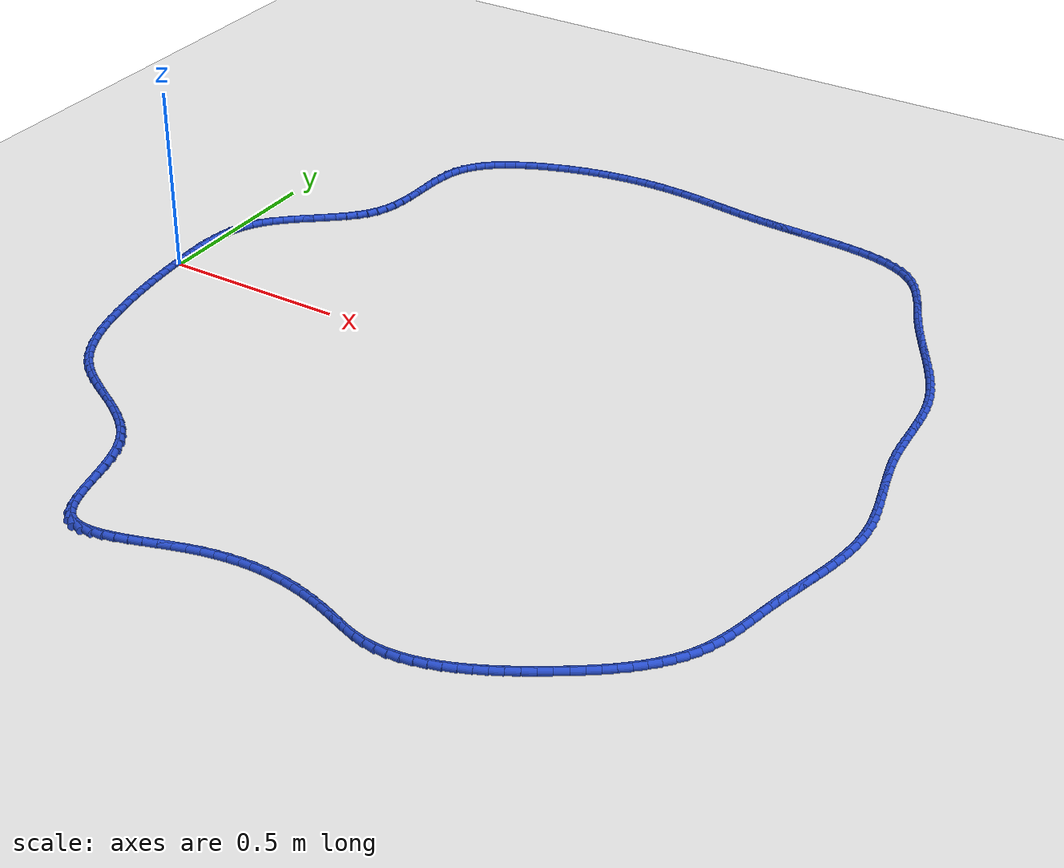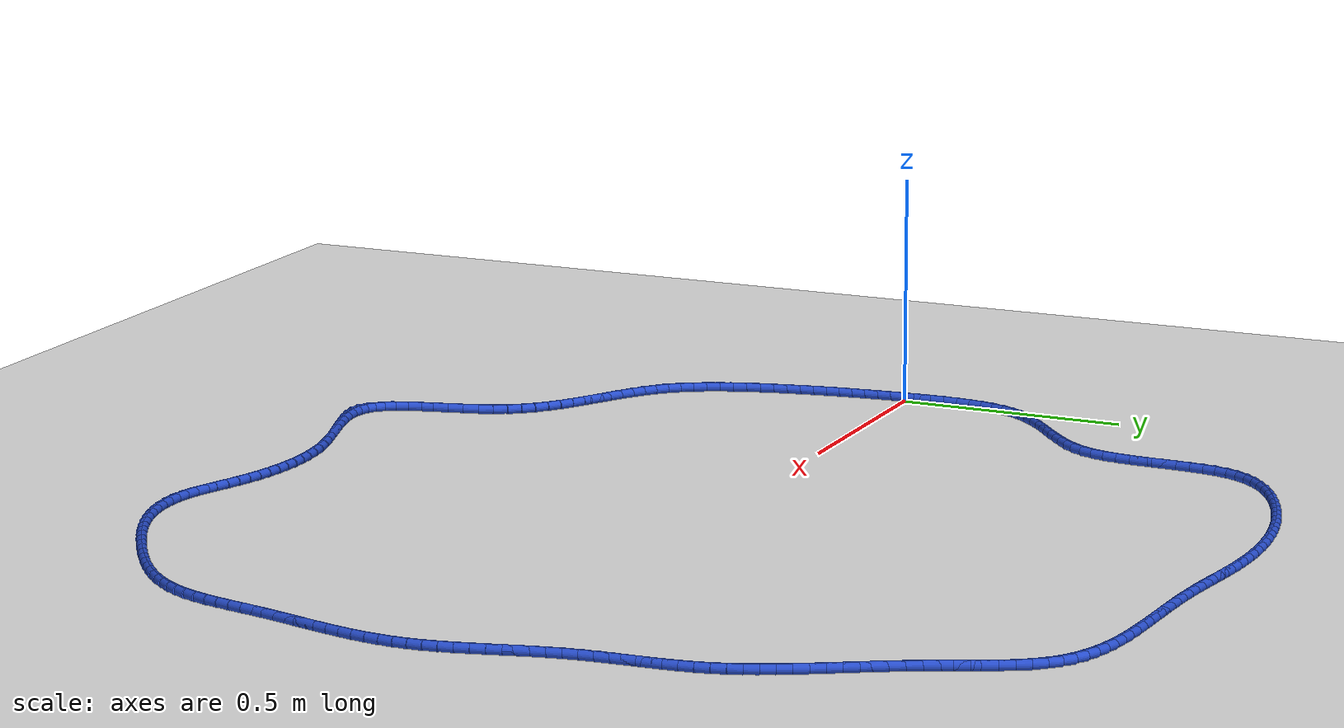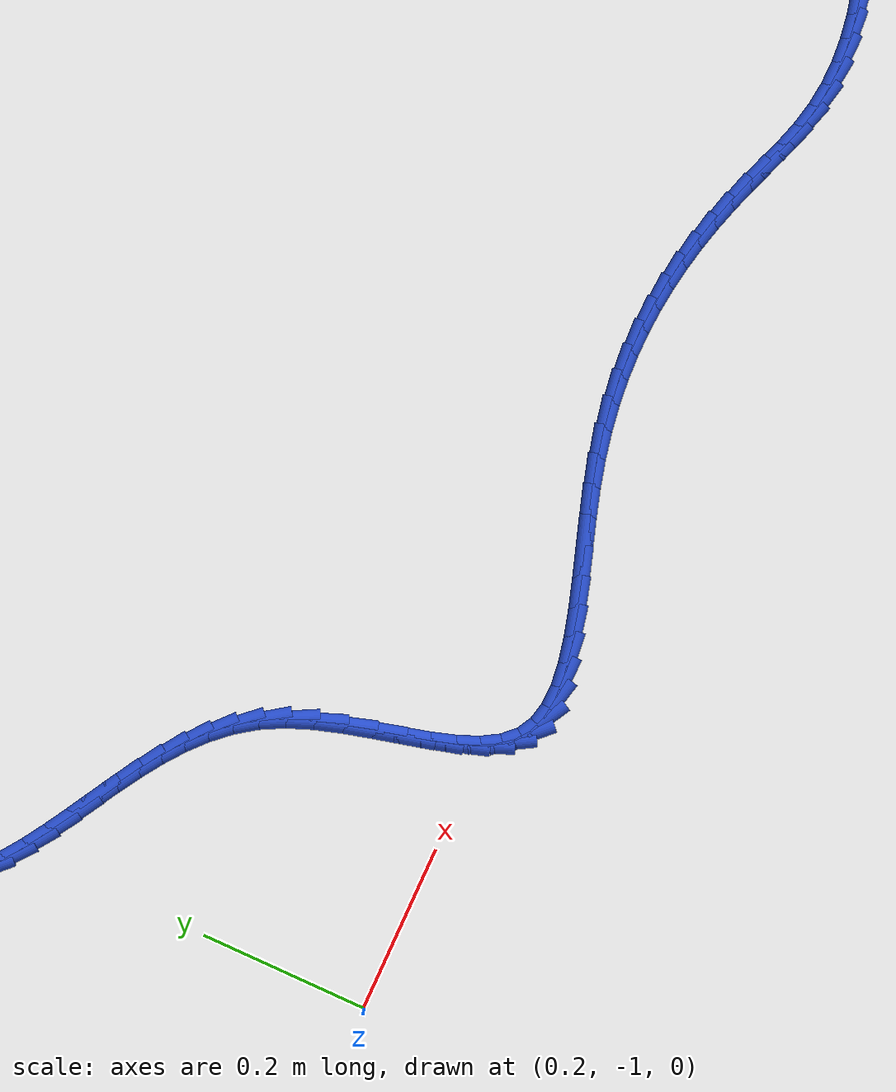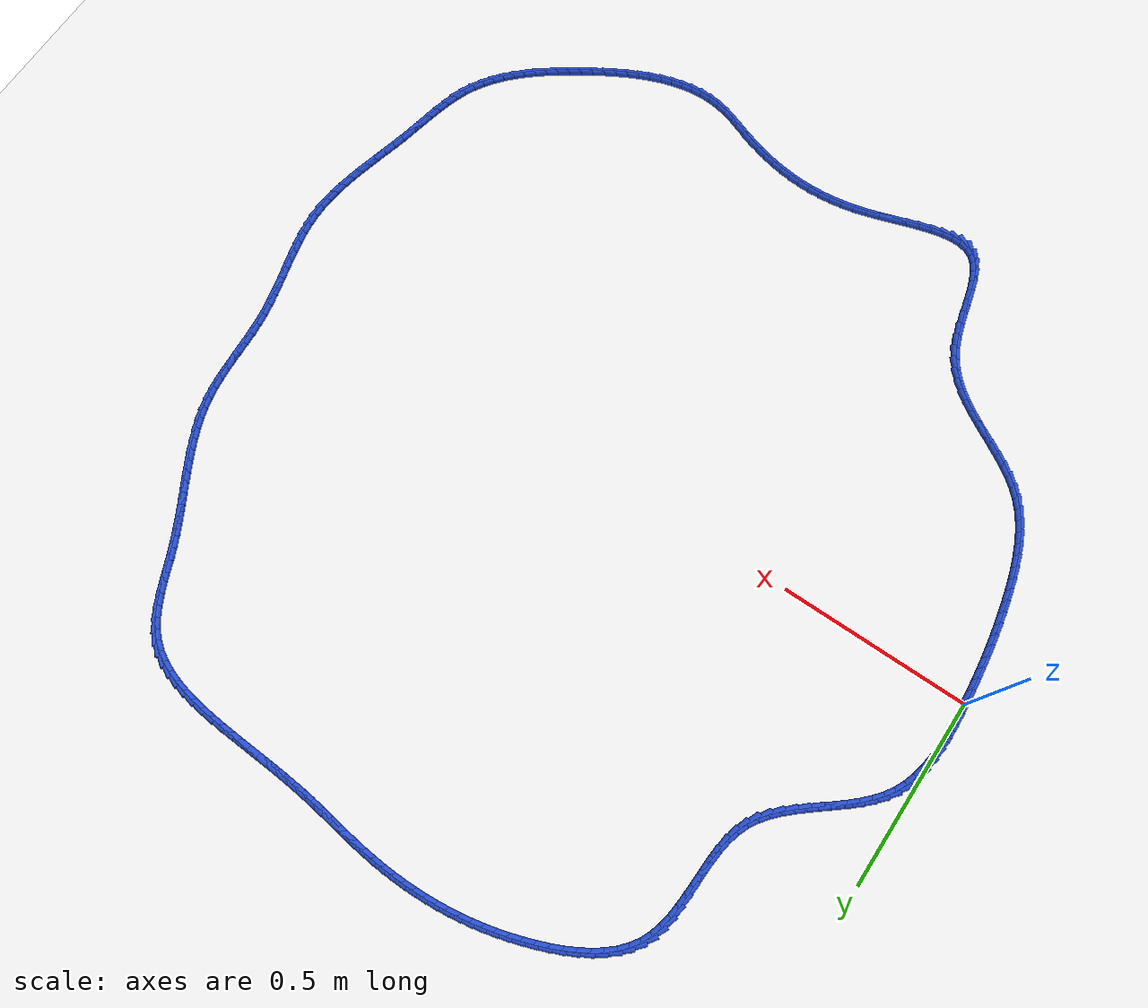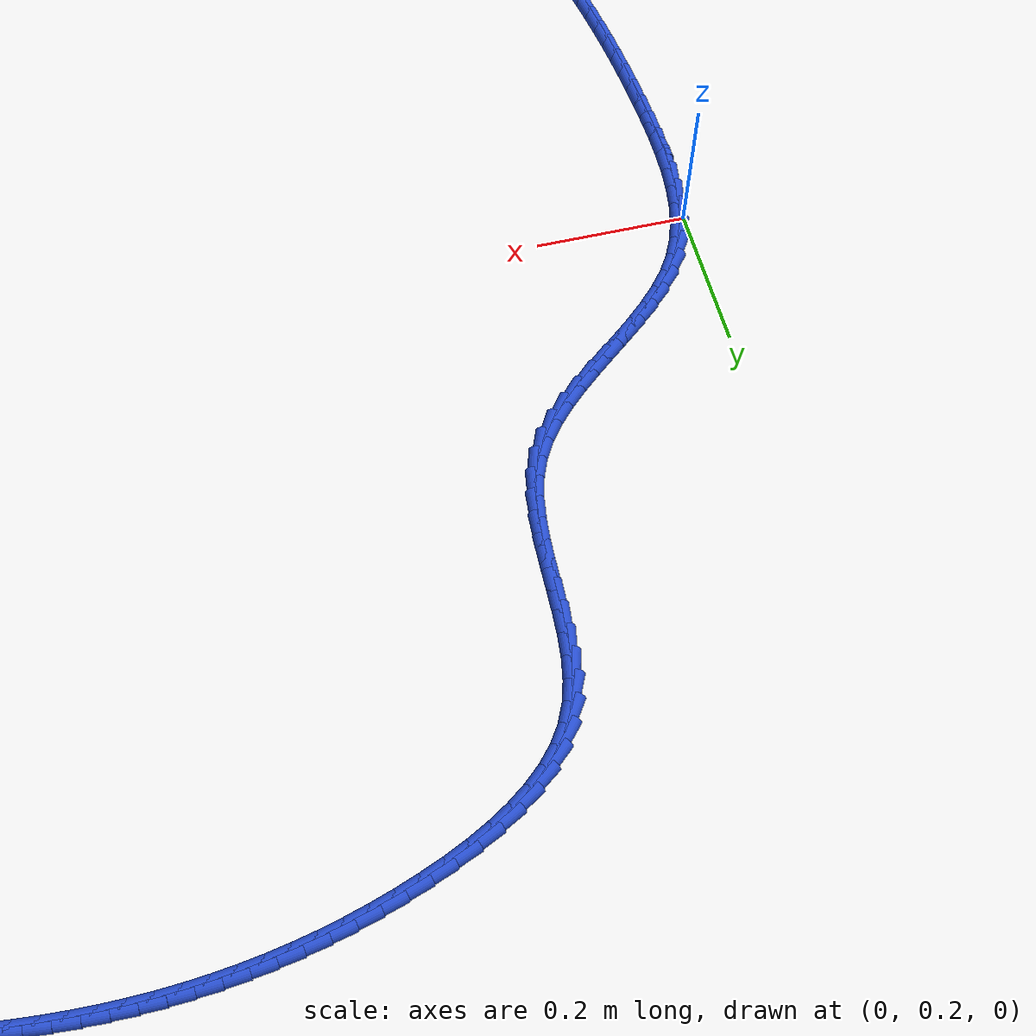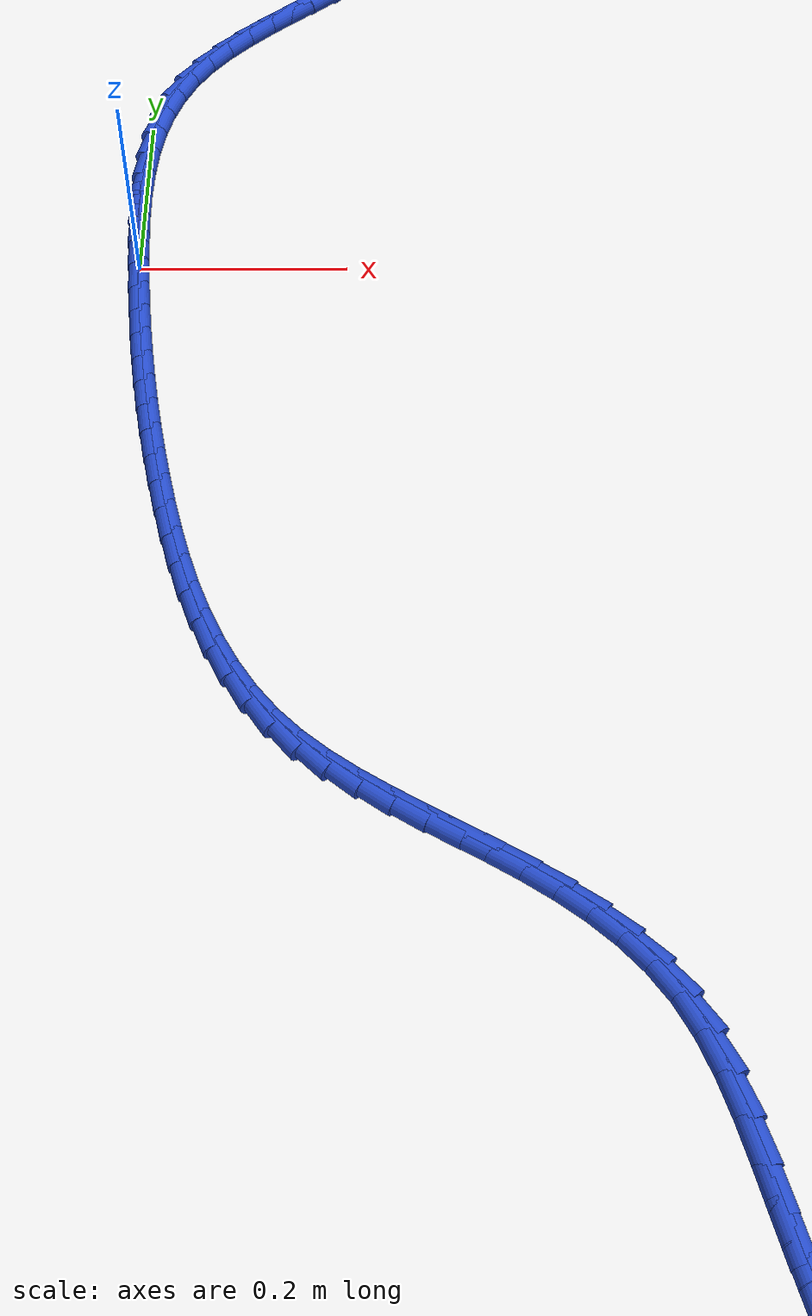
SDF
<sdf version="1.6">
 <world name="default">
  <light name="sun" type="directional">
   <pose>0 0 10 0 -0 0</pose>
   <diffuse>0.8 0.8 0.8 1</diffuse>
   <specular>0.2 0.2 0.2 1</specular>
   <attenuation>
    <range>1000</range>
    <constant>0.9</constant>
    <linear>0.01</linear>
    <quadratic>0.001</quadratic>
   </attenuation>
   <direction>-0.5 0.1 -0.9</direction>
  </light>
  <model name="ground_plane">
   <static>1</static>
   <link name="link">
    <collision name="collision">
     <geometry><plane><normal>0 0 1</normal><size>100 100</size></plane></geometry>
     <surface><friction><ode><mu>100</mu><mu2>50</mu2></ode></friction></surface>
    </collision>
    <visual name="visual">
     <cast_shadows>0</cast_shadows>
     <geometry><plane><normal>0 0 1</normal><size>100 100</size></plane></geometry>
     <material>
      <script><uri>file://media/materials/scripts/gazebo.material</uri><name>Gazebo/WhiteGlow</name></script>
     </material>
    </visual>
   </link>
  </model>
  <gravity>0 0 -9.8</gravity>
  <magnetic_field>6e-06 2.3e-05 -4.2e-05</magnetic_field>
  <atmosphere type="adiabatic"/>
  <physics name="default_physics" default="0" type="ode">
   <max_step_size>0.001</max_step_size>
   <real_time_factor>1</real_time_factor>
   <real_time_update_rate>1000</real_time_update_rate>
  </physics>
  <scene><ambient>0.4 0.4 0.4 1</ambient><background>0.7 0.7 0.7 1</background><shadows>1</shadows></scene>
  <spherical_coordinates>
   <surface_model>EARTH_WGS84</surface_model>
   <latitude_deg>0</latitude_deg>
   <longitude_deg>0</longitude_deg>
   <elevation>0</elevation>
   <heading_deg>0</heading_deg>
  </spherical_coordinates>
  <model name="line">
   <link name="link_0">
    <pose>-1.8431436932253575e-17 3.469446951953614e-17 0.01 0 1.57 -1.5108364362840674</pose>
    <collision name="collision">
     <geometry><cylinder><radius>0.01</radius><length>0.08</length></cylinder></geometry>
    </collision>
    <visual name="visual">
     <material>
      <script><name>Gazebo/Blue</name><uri>file://media/materials/scripts/gazebo.material</uri></script>
     </material>
     <geometry><cylinder><radius>0.01</radius><length>0.08</length></cylinder></geometry>
    </visual>
   </link>
   <link name="link_1">
    <pose>-0.0018603580479526589 0.030989517353228024 0.01 0 1.57 -1.5329625650588325</pose>
    <collision name="collision">
     <geometry><cylinder><radius>0.01</radius><length>0.08</length></cylinder></geometry>
    </collision>
    <visual name="visual">
     <material>
      <script><name>Gazebo/Blue</name><uri>file://media/materials/scripts/gazebo.material</uri></script>
     </material>
     <geometry><cylinder><radius>0.01</radius><length>0.08</length></cylinder></geometry>
    </visual>
   </link>
   <link name="link_2">
    <pose>-0.003043777788168357 0.062254054253526286 0.01 0 1.57 -1.5652332365933455</pose>
    <collision name="collision">
     <geometry><cylinder><radius>0.01</radius><length>0.08</length></cylinder></geometry>
    </collision>
    <visual name="visual">
     <material>
      <script><name>Gazebo/Blue</name><uri>file://media/materials/scripts/gazebo.material</uri></script>
     </material>
     <geometry><cylinder><radius>0.01</radius><length>0.08</length></cylinder></geometry>
    </visual>
   </link>
   <link name="link_3">
    <pose>-0.00321780486593825 0.09353617915164875 0.01 0 1.57 1.5331937595008902</pose>
    <collision name="collision">
     <geometry><cylinder><radius>0.01</radius><length>0.08</length></cylinder></geometry>
    </collision>
    <visual name="visual">
     <material>
      <script><name>Gazebo/Blue</name><uri>file://media/materials/scripts/gazebo.material</uri></script>
     </material>
     <geometry><cylinder><radius>0.01</radius><length>0.08</length></cylinder></geometry>
    </visual>
   </link>
   <link name="link_4">
    <pose>-0.002049984926553456 0.12457846049834907 0.01 0 1.57 1.478016462440718</pose>
    <collision name="collision">
     <geometry><cylinder><radius>0.01</radius><length>0.08</length></cylinder></geometry>
    </collision>
    <visual name="visual">
     <material>
      <script><name>Gazebo/Blue</name><uri>file://media/materials/scripts/gazebo.material</uri></script>
     </material>
     <geometry><cylinder><radius>0.01</radius><length>0.08</length></cylinder></geometry>
    </visual>
   </link>
   <link name="link_5">
    <pose>0.0007921363846948824 0.15512346674438132 0.01 0 1.57 1.4094443238107668</pose>
    <collision name="collision">
     <geometry><cylinder><radius>0.01</radius><length>0.08</length></cylinder></geometry>
    </collision>
    <visual name="visual">
     <material>
      <script><name>Gazebo/Blue</name><uri>file://media/materials/scripts/gazebo.material</uri></script>
     </material>
     <geometry><cylinder><radius>0.01</radius><length>0.08</length></cylinder></geometry>
    </visual>
   </link>
   <link name="link_6">
    <pose>0.005641013422515643 0.18491376634049916 0.01 0 1.57 1.3260287247107136</pose>
    <collision name="collision">
     <geometry><cylinder><radius>0.01</radius><length>0.08</length></cylinder></geometry>
    </collision>
    <visual name="visual">
     <material>
      <script><name>Gazebo/Blue</name><uri>file://media/materials/scripts/gazebo.material</uri></script>
     </material>
     <geometry><cylinder><radius>0.01</radius><length>0.08</length></cylinder></geometry>
    </visual>
   </link>
   <link name="link_7">
    <pose>0.012829100541617695 0.21369192773745646 0.01 0 1.57 1.226636240695132</pose>
    <collision name="collision">
     <geometry><cylinder><radius>0.01</radius><length>0.08</length></cylinder></geometry>
    </collision>
    <visual name="visual">
     <material>
      <script><name>Gazebo/Blue</name><uri>file://media/materials/scripts/gazebo.material</uri></script>
     </material>
     <geometry><cylinder><radius>0.01</radius><length>0.08</length></cylinder></geometry>
    </visual>
   </link>
   <link name="link_8">
    <pose>0.02268885209670991 0.2412005193860071 0.01 0 1.57 1.1110644961267344</pose>
    <collision name="collision">
     <geometry><cylinder><radius>0.01</radius><length>0.08</length></cylinder></geometry>
    </collision>
    <visual name="visual">
     <material>
      <script><name>Gazebo/Blue</name><uri>file://media/materials/scripts/gazebo.material</uri></script>
     </material>
     <geometry><cylinder><radius>0.01</radius><length>0.08</length></cylinder></geometry>
    </visual>
   </link>
   <link name="link_9">
    <pose>0.035552722442501156 0.2671821097369049 0.01 0 1.57 0.9852909173942257</pose>
    <collision name="collision">
     <geometry><cylinder><radius>0.01</radius><length>0.08</length></cylinder></geometry>
    </collision>
    <visual name="visual">
     <material>
      <script><name>Gazebo/Blue</name><uri>file://media/materials/scripts/gazebo.material</uri></script>
     </material>
     <geometry><cylinder><radius>0.01</radius><length>0.08</length></cylinder></geometry>
    </visual>
   </link>
   <link name="link_10">
    <pose>0.05164222435093219 0.29144743432178616 0.01 0 1.57 0.8764779752378719</pose>
    <collision name="collision">
     <geometry><cylinder><radius>0.01</radius><length>0.08</length></cylinder></geometry>
    </collision>
    <visual name="visual">
     <material>
      <script><name>Gazebo/Blue</name><uri>file://media/materials/scripts/gazebo.material</uri></script>
     </material>
     <geometry><cylinder><radius>0.01</radius><length>0.08</length></cylinder></geometry>
    </visual>
   </link>
   <link name="link_11">
    <pose>0.0705706473687541 0.3141809460896137 0.01 0 1.57 0.7933697692231528</pose>
    <collision name="collision">
     <geometry><cylinder><radius>0.01</radius><length>0.08</length></cylinder></geometry>
    </collision>
    <visual name="visual">
     <material>
      <script><name>Gazebo/Blue</name><uri>file://media/materials/scripts/gazebo.material</uri></script>
     </material>
     <geometry><cylinder><radius>0.01</radius><length>0.08</length></cylinder></geometry>
    </visual>
   </link>
   <link name="link_12">
    <pose>0.09174392037291848 0.33569450893119346 0.01 0 1.57 0.7343645125878144</pose>
    <collision name="collision">
     <geometry><cylinder><radius>0.01</radius><length>0.08</length></cylinder></geometry>
    </collision>
    <visual name="visual">
     <material>
      <script><name>Gazebo/Blue</name><uri>file://media/materials/scripts/gazebo.material</uri></script>
     </material>
     <geometry><cylinder><radius>0.01</radius><length>0.08</length></cylinder></geometry>
    </visual>
   </link>
   <link name="link_13">
    <pose>0.11456779636597547 0.3563000948018122 0.01 0 1.57 0.6974355412849094</pose>
    <collision name="collision">
     <geometry><cylinder><radius>0.01</radius><length>0.08</length></cylinder></geometry>
    </collision>
    <visual name="visual">
     <material>
      <script><name>Gazebo/Blue</name><uri>file://media/materials/scripts/gazebo.material</uri></script>
     </material>
     <geometry><cylinder><radius>0.01</radius><length>0.08</length></cylinder></geometry>
    </visual>
   </link>
   <link name="link_14">
    <pose>0.1384480283504753 0.3763096756567571 0.01 0 1.57 0.6810134815637398</pose>
    <collision name="collision">
     <geometry><cylinder><radius>0.01</radius><length>0.08</length></cylinder></geometry>
    </collision>
    <visual name="visual">
     <material>
      <script><name>Gazebo/Blue</name><uri>file://media/materials/scripts/gazebo.material</uri></script>
     </material>
     <geometry><cylinder><radius>0.01</radius><length>0.08</length></cylinder></geometry>
    </visual>
   </link>
   <link name="link_15">
    <pose>0.16279036932896798 0.39603522345131503 0.01 0 1.57 0.6843706243961865</pose>
    <collision name="collision">
     <geometry><cylinder><radius>0.01</radius><length>0.08</length></cylinder></geometry>
    </collision>
    <visual name="visual">
     <material>
      <script><name>Gazebo/Blue</name><uri>file://media/materials/scripts/gazebo.material</uri></script>
     </material>
     <geometry><cylinder><radius>0.01</radius><length>0.08</length></cylinder></geometry>
    </visual>
   </link>
   <link name="link_16">
    <pose>0.18700057230400366 0.41578871014077284 0.01 0 1.57 0.707751987061713</pose>
    <collision name="collision">
     <geometry><cylinder><radius>0.01</radius><length>0.08</length></cylinder></geometry>
    </collision>
    <visual name="visual">
     <material>
      <script><name>Gazebo/Blue</name><uri>file://media/materials/scripts/gazebo.material</uri></script>
     </material>
     <geometry><cylinder><radius>0.01</radius><length>0.08</length></cylinder></geometry>
    </visual>
   </link>
   <link name="link_17">
    <pose>0.21048439027813257 0.4358821076804177 0.01 0 1.57 0.7523652915889322</pose>
    <collision name="collision">
     <geometry><cylinder><radius>0.01</radius><length>0.08</length></cylinder></geometry>
    </collision>
    <visual name="visual">
     <material>
      <script><name>Gazebo/Blue</name><uri>file://media/materials/scripts/gazebo.material</uri></script>
     </material>
     <geometry><cylinder><radius>0.01</radius><length>0.08</length></cylinder></geometry>
    </visual>
   </link>
   <link name="link_18">
    <pose>0.2326475762539047 0.45662738802553626 0.01 0 1.57 0.8202010065220533</pose>
    <collision name="collision">
     <geometry><cylinder><radius>0.01</radius><length>0.08</length></cylinder></geometry>
    </collision>
    <visual name="visual">
     <material>
      <script><name>Gazebo/Blue</name><uri>file://media/materials/scripts/gazebo.material</uri></script>
     </material>
     <geometry><cylinder><radius>0.01</radius><length>0.08</length></cylinder></geometry>
    </visual>
   </link>
   <link name="link_19">
    <pose>0.2528958832338702 0.4783365231314155 0.01 0 1.57 0.9135052787877467</pose>
    <collision name="collision">
     <geometry><cylinder><radius>0.01</radius><length>0.08</length></cylinder></geometry>
    </collision>
    <visual name="visual">
     <material>
      <script><name>Gazebo/Blue</name><uri>file://media/materials/scripts/gazebo.material</uri></script>
     </material>
     <geometry><cylinder><radius>0.01</radius><length>0.08</length></cylinder></geometry>
    </visual>
   </link>
   <link name="link_20">
    <pose>0.27063506422057937 0.5013214849533426 0.01 0 1.57 1.0336102357399797</pose>
    <collision name="collision">
     <geometry><cylinder><radius>0.01</radius><length>0.08</length></cylinder></geometry>
    </collision>
    <visual name="visual">
     <material>
      <script><name>Gazebo/Blue</name><uri>file://media/materials/scripts/gazebo.material</uri></script>
     </material>
     <geometry><cylinder><radius>0.01</radius><length>0.08</length></cylinder></geometry>
    </visual>
   </link>
   <link name="link_21">
    <pose>0.285270872216582 0.5258942454466042 0.01 0 1.57 1.1759216926767986</pose>
    <collision name="collision">
     <geometry><cylinder><radius>0.01</radius><length>0.08</length></cylinder></geometry>
    </collision>
    <visual name="visual">
     <material>
      <script><name>Gazebo/Blue</name><uri>file://media/materials/scripts/gazebo.material</uri></script>
     </material>
     <geometry><cylinder><radius>0.01</radius><length>0.08</length></cylinder></geometry>
    </visual>
   </link>
   <link name="link_22">
    <pose>0.2962867510966842 0.5523261369084196 0.01 0 1.57 1.3056099540510582</pose>
    <collision name="collision">
     <geometry><cylinder><radius>0.01</radius><length>0.08</length></cylinder></geometry>
    </collision>
    <visual name="visual">
     <material>
      <script><name>Gazebo/Blue</name><uri>file://media/materials/scripts/gazebo.material</uri></script>
     </material>
     <geometry><cylinder><radius>0.01</radius><length>0.08</length></cylinder></geometry>
    </visual>
   </link>
   <link name="link_23">
    <pose>0.30393461937423066 0.5804865068772168 0.01 0 1.57 1.404038919432104</pose>
    <collision name="collision">
     <geometry><cylinder><radius>0.01</radius><length>0.08</length></cylinder></geometry>
    </collision>
    <visual name="visual">
     <material>
      <script><name>Gazebo/Blue</name><uri>file://media/materials/scripts/gazebo.material</uri></script>
     </material>
     <geometry><cylinder><radius>0.01</radius><length>0.08</length></cylinder></geometry>
    </visual>
   </link>
   <link name="link_24">
    <pose>0.30890492336611636 0.6100153114652229 0.01 0 1.57 1.4732405392733319</pose>
    <collision name="collision">
     <geometry><cylinder><radius>0.01</radius><length>0.08</length></cylinder></geometry>
    </collision>
    <visual name="visual">
     <material>
      <script><name>Gazebo/Blue</name><uri>file://media/materials/scripts/gazebo.material</uri></script>
     </material>
     <geometry><cylinder><radius>0.01</radius><length>0.08</length></cylinder></geometry>
    </visual>
   </link>
   <link name="link_25">
    <pose>0.31189322833100325 0.6405498290950341 0.01 0 1.57 1.516263943865348</pose>
    <collision name="collision">
     <geometry><cylinder><radius>0.01</radius><length>0.08</length></cylinder></geometry>
    </collision>
    <visual name="visual">
     <material>
      <script><name>Gazebo/Blue</name><uri>file://media/materials/scripts/gazebo.material</uri></script>
     </material>
     <geometry><cylinder><radius>0.01</radius><length>0.08</length></cylinder></geometry>
    </visual>
   </link>
   <link name="link_26">
    <pose>0.31359509952755305 0.6717273381892465 0.01 0 1.57 1.5354937356088845</pose>
    <collision name="collision">
     <geometry><cylinder><radius>0.01</radius><length>0.08</length></cylinder></geometry>
    </collision>
    <visual name="visual">
     <material>
      <script><name>Gazebo/Blue</name><uri>file://media/materials/scripts/gazebo.material</uri></script>
     </material>
     <geometry><cylinder><radius>0.01</radius><length>0.08</length></cylinder></geometry>
    </visual>
   </link>
   <link name="link_27">
    <pose>0.3147061022144279 0.7031851171704563 0.01 0 1.57 1.5320687118209877</pose>
    <collision name="collision">
     <geometry><cylinder><radius>0.01</radius><length>0.08</length></cylinder></geometry>
    </collision>
    <visual name="visual">
     <material>
      <script><name>Gazebo/Blue</name><uri>file://media/materials/scripts/gazebo.material</uri></script>
     </material>
     <geometry><cylinder><radius>0.01</radius><length>0.08</length></cylinder></geometry>
    </visual>
   </link>
   <link name="link_28">
    <pose>0.31592180165028955 0.7345604444612596 0.01 0 1.57 1.5057105211670865</pose>
    <collision name="collision">
     <geometry><cylinder><radius>0.01</radius><length>0.08</length></cylinder></geometry>
    </collision>
    <visual name="visual">
     <material>
      <script><name>Gazebo/Blue</name><uri>file://media/materials/scripts/gazebo.material</uri></script>
     </material>
     <geometry><cylinder><radius>0.01</radius><length>0.08</length></cylinder></geometry>
    </visual>
   </link>
   <link name="link_29">
    <pose>0.31793776309379995 0.7654905984842523 0.01 0 1.57 1.4547357579366387</pose>
    <collision name="collision">
     <geometry><cylinder><radius>0.01</radius><length>0.08</length></cylinder></geometry>
    </collision>
    <visual name="visual">
     <material>
      <script><name>Gazebo/Blue</name><uri>file://media/materials/scripts/gazebo.material</uri></script>
     </material>
     <geometry><cylinder><radius>0.01</radius><length>0.08</length></cylinder></geometry>
    </visual>
   </link>
   <link name="link_30">
    <pose>0.321449551803621 0.7956128576620309 0.01 0 1.57 1.3762967613827837</pose>
    <collision name="collision">
     <geometry><cylinder><radius>0.01</radius><length>0.08</length></cylinder></geometry>
    </collision>
    <visual name="visual">
     <material>
      <script><name>Gazebo/Blue</name><uri>file://media/materials/scripts/gazebo.material</uri></script>
     </material>
     <geometry><cylinder><radius>0.01</radius><length>0.08</length></cylinder></geometry>
    </visual>
   </link>
   <link name="link_31">
    <pose>0.3271527330384145 0.8245645004171915 0.01 0 1.57 1.2671833256716287</pose>
    <collision name="collision">
     <geometry><cylinder><radius>0.01</radius><length>0.08</length></cylinder></geometry>
    </collision>
    <visual name="visual">
     <material>
      <script><name>Gazebo/Blue</name><uri>file://media/materials/scripts/gazebo.material</uri></script>
     </material>
     <geometry><cylinder><radius>0.01</radius><length>0.08</length></cylinder></geometry>
    </visual>
   </link>
   <link name="link_32">
    <pose>0.3357428720568426 0.8519828051723302 0.01 0 1.57 1.1260675082765381</pose>
    <collision name="collision">
     <geometry><cylinder><radius>0.01</radius><length>0.08</length></cylinder></geometry>
    </collision>
    <visual name="visual">
     <material>
      <script><name>Gazebo/Blue</name><uri>file://media/materials/scripts/gazebo.material</uri></script>
     </material>
     <geometry><cylinder><radius>0.01</radius><length>0.08</length></cylinder></geometry>
    </visual>
   </link>
   <link name="link_33">
    <pose>0.34790756262974987 0.8775082929686959 0.01 0 1.57 0.9725308441972007</pose>
    <collision name="collision">
     <geometry><cylinder><radius>0.01</radius><length>0.08</length></cylinder></geometry>
    </collision>
    <visual name="visual">
     <material>
      <script><name>Gazebo/Blue</name><uri>file://media/materials/scripts/gazebo.material</uri></script>
     </material>
     <geometry><cylinder><radius>0.01</radius><length>0.08</length></cylinder></geometry>
    </visual>
   </link>
   <link name="link_34">
    <pose>0.3638928426894296 0.9009610996485867 0.01 0 1.57 0.8363248654371503</pose>
    <collision name="collision">
     <geometry><cylinder><radius>0.01</radius><length>0.08</length></cylinder></geometry>
    </collision>
    <visual name="visual">
     <material>
      <script><name>Gazebo/Blue</name><uri>file://media/materials/scripts/gazebo.material</uri></script>
     </material>
     <geometry><cylinder><radius>0.01</radius><length>0.08</length></cylinder></geometry>
    </visual>
   </link>
   <link name="link_35">
    <pose>0.38328066409595246 0.9224314960572341 0.01 0 1.57 0.7206730497777499</pose>
    <collision name="collision">
     <geometry><cylinder><radius>0.01</radius><length>0.08</length></cylinder></geometry>
    </collision>
    <visual name="visual">
     <material>
      <script><name>Gazebo/Blue</name><uri>file://media/materials/scripts/gazebo.material</uri></script>
     </material>
     <geometry><cylinder><radius>0.01</radius><length>0.08</length></cylinder></geometry>
    </visual>
   </link>
   <link name="link_36">
    <pose>0.40559816429354234 0.9420320502886818 0.01 0 1.57 0.6241764843903241</pose>
    <collision name="collision">
     <geometry><cylinder><radius>0.01</radius><length>0.08</length></cylinder></geometry>
    </collision>
    <visual name="visual">
     <material>
      <script><name>Gazebo/Blue</name><uri>file://media/materials/scripts/gazebo.material</uri></script>
     </material>
     <geometry><cylinder><radius>0.01</radius><length>0.08</length></cylinder></geometry>
    </visual>
   </link>
   <link name="link_37">
    <pose>0.4303724807264235 0.9598753304369729 0.01 0 1.57 0.5443564939224657</pose>
    <collision name="collision">
     <geometry><cylinder><radius>0.01</radius><length>0.08</length></cylinder></geometry>
    </collision>
    <visual name="visual">
     <material>
      <script><name>Gazebo/Blue</name><uri>file://media/materials/scripts/gazebo.material</uri></script>
     </material>
     <geometry><cylinder><radius>0.01</radius><length>0.08</length></cylinder></geometry>
    </visual>
   </link>
   <link name="link_38">
    <pose>0.4571307508388197 0.9760739045961517 0.01 0 1.57 0.47858237269939863</pose>
    <collision name="collision">
     <geometry><cylinder><radius>0.01</radius><length>0.08</length></cylinder></geometry>
    </collision>
    <visual name="visual">
     <material>
      <script><name>Gazebo/Blue</name><uri>file://media/materials/scripts/gazebo.material</uri></script>
     </material>
     <geometry><cylinder><radius>0.01</radius><length>0.08</length></cylinder></geometry>
    </visual>
   </link>
   <link name="link_39">
    <pose>0.4854001120749556 0.990740340860262 0.01 0 1.57 0.42451123222440756</pose>
    <collision name="collision">
     <geometry><cylinder><radius>0.01</radius><length>0.08</length></cylinder></geometry>
    </collision>
    <visual name="visual">
     <material>
      <script><name>Gazebo/Blue</name><uri>file://media/materials/scripts/gazebo.material</uri></script>
     </material>
     <geometry><cylinder><radius>0.01</radius><length>0.08</length></cylinder></geometry>
    </visual>
   </link>
   <link name="link_40">
    <pose>0.514707701879055 1.0039872073233473 0.01 0 1.57 0.3802374632442807</pose>
    <collision name="collision">
     <geometry><cylinder><radius>0.01</radius><length>0.08</length></cylinder></geometry>
    </collision>
    <visual name="visual">
     <material>
      <script><name>Gazebo/Blue</name><uri>file://media/materials/scripts/gazebo.material</uri></script>
     </material>
     <geometry><cylinder><radius>0.01</radius><length>0.08</length></cylinder></geometry>
    </visual>
   </link>
   <link name="link_41">
    <pose>0.5445806576953421 1.0159270720794515 0.01 0 1.57 0.3440077576885174</pose>
    <collision name="collision">
     <geometry><cylinder><radius>0.01</radius><length>0.08</length></cylinder></geometry>
    </collision>
    <visual name="visual">
     <material>
      <script><name>Gazebo/Blue</name><uri>file://media/materials/scripts/gazebo.material</uri></script>
     </material>
     <geometry><cylinder><radius>0.01</radius><length>0.08</length></cylinder></geometry>
    </visual>
   </link>
   <link name="link_42">
    <pose>0.5745652162206966 1.02666911667889 0.01 0 1.57 0.31079603707561204</pose>
    <collision name="collision">
     <geometry><cylinder><radius>0.01</radius><length>0.08</length></cylinder></geometry>
    </collision>
    <visual name="visual">
     <material>
      <script><name>Gazebo/Blue</name><uri>file://media/materials/scripts/gazebo.material</uri></script>
     </material>
     <geometry><cylinder><radius>0.01</radius><length>0.08</length></cylinder></geometry>
    </visual>
   </link>
   <link name="link_43">
    <pose>0.6044726120363393 1.0362755351306763 0.01 0 1.57 0.2775009803824403</pose>
    <collision name="collision">
     <geometry><cylinder><radius>0.01</radius><length>0.08</length></cylinder></geometry>
    </collision>
    <visual name="visual">
     <material>
      <script><name>Gazebo/Blue</name><uri>file://media/materials/scripts/gazebo.material</uri></script>
     </material>
     <geometry><cylinder><radius>0.01</radius><length>0.08</length></cylinder></geometry>
    </visual>
   </link>
   <link name="link_44">
    <pose>0.6343079424751948 1.044774147078624 0.01 0 1.57 0.24417680208551315</pose>
    <collision name="collision">
     <geometry><cylinder><radius>0.01</radius><length>0.08</length></cylinder></geometry>
    </collision>
    <visual name="visual">
     <material>
      <script><name>Gazebo/Blue</name><uri>file://media/materials/scripts/gazebo.material</uri></script>
     </material>
     <geometry><cylinder><radius>0.01</radius><length>0.08</length></cylinder></geometry>
    </visual>
   </link>
   <link name="link_45">
    <pose>0.6640807399340121 1.0521919857725537 0.01 0 1.57 0.21095083937448827</pose>
    <collision name="collision">
     <geometry><cylinder><radius>0.01</radius><length>0.08</length></cylinder></geometry>
    </collision>
    <visual name="visual">
     <material>
      <script><name>Gazebo/Blue</name><uri>file://media/materials/scripts/gazebo.material</uri></script>
     </material>
     <geometry><cylinder><radius>0.01</radius><length>0.08</length></cylinder></geometry>
    </visual>
   </link>
   <link name="link_46">
    <pose>0.6938005368095398 1.0585560844622863 0.01 0 1.57 0.17795104378243407</pose>
    <collision name="collision">
     <geometry><cylinder><radius>0.01</radius><length>0.08</length></cylinder></geometry>
    </collision>
    <visual name="visual">
     <material>
      <script><name>Gazebo/Blue</name><uri>file://media/materials/scripts/gazebo.material</uri></script>
     </material>
     <geometry><cylinder><radius>0.01</radius><length>0.08</length></cylinder></geometry>
    </visual>
   </link>
   <link name="link_47">
    <pose>0.7234768654985271 1.0638934763976426 0.01 0 1.57 0.14530364527494383</pose>
    <collision name="collision">
     <geometry><cylinder><radius>0.01</radius><length>0.08</length></cylinder></geometry>
    </collision>
    <visual name="visual">
     <material>
      <script><name>Gazebo/Blue</name><uri>file://media/materials/scripts/gazebo.material</uri></script>
     </material>
     <geometry><cylinder><radius>0.01</radius><length>0.08</length></cylinder></geometry>
    </visual>
   </link>
   <link name="link_48">
    <pose>0.7531192583977223 1.0682311948284429 0.01 0 1.57 0.11313090019355598</pose>
    <collision name="collision">
     <geometry><cylinder><radius>0.01</radius><length>0.08</length></cylinder></geometry>
    </collision>
    <visual name="visual">
     <material>
      <script><name>Gazebo/Blue</name><uri>file://media/materials/scripts/gazebo.material</uri></script>
     </material>
     <geometry><cylinder><radius>0.01</radius><length>0.08</length></cylinder></geometry>
    </visual>
   </link>
   <link name="link_49">
    <pose>0.7827372479038746 1.0715962730045077 0.01 0 1.57 0.08154902442503599</pose>
    <collision name="collision">
     <geometry><cylinder><radius>0.01</radius><length>0.08</length></cylinder></geometry>
    </collision>
    <visual name="visual">
     <material>
      <script><name>Gazebo/Blue</name><uri>file://media/materials/scripts/gazebo.material</uri></script>
     </material>
     <geometry><cylinder><radius>0.01</radius><length>0.08</length></cylinder></geometry>
    </visual>
   </link>
   <link name="link_50">
    <pose>0.8123403664137328 1.074015744175658 0.01 0 1.57 0.0506663976457649</pose>
    <collision name="collision">
     <geometry><cylinder><radius>0.01</radius><length>0.08</length></cylinder></geometry>
    </collision>
    <visual name="visual">
     <material>
      <script><name>Gazebo/Blue</name><uri>file://media/materials/scripts/gazebo.material</uri></script>
     </material>
     <geometry><cylinder><radius>0.01</radius><length>0.08</length></cylinder></geometry>
    </visual>
   </link>
   <link name="link_51">
    <pose>0.8419381463240457 1.0755166415917141 0.01 0 1.57 0.020582102683906263</pose>
    <collision name="collision">
     <geometry><cylinder><radius>0.01</radius><length>0.08</length></cylinder></geometry>
    </collision>
    <visual name="visual">
     <material>
      <script><name>Gazebo/Blue</name><uri>file://media/materials/scripts/gazebo.material</uri></script>
     </material>
     <geometry><cylinder><radius>0.01</radius><length>0.08</length></cylinder></geometry>
    </visual>
   </link>
   <link name="link_52">
    <pose>0.871540120031562 1.0761259985024962 0.01 0 1.57 -0.008615161315899237</pose>
    <collision name="collision">
     <geometry><cylinder><radius>0.01</radius><length>0.08</length></cylinder></geometry>
    </collision>
    <visual name="visual">
     <material>
      <script><name>Gazebo/Blue</name><uri>file://media/materials/scripts/gazebo.material</uri></script>
     </material>
     <geometry><cylinder><radius>0.01</radius><length>0.08</length></cylinder></geometry>
    </visual>
   </link>
   <link name="link_53">
    <pose>0.9011558199330305 1.0758708481578256 0.01 0 1.57 -0.036847779217226824</pose>
    <collision name="collision">
     <geometry><cylinder><radius>0.01</radius><length>0.08</length></cylinder></geometry>
    </collision>
    <visual name="visual">
     <material>
      <script><name>Gazebo/Blue</name><uri>file://media/materials/scripts/gazebo.material</uri></script>
     </material>
     <geometry><cylinder><radius>0.01</radius><length>0.08</length></cylinder></geometry>
    </visual>
   </link>
   <link name="link_54">
    <pose>0.9307947784252002 1.0747782238075227 0.01 0 1.57 -0.06404954492907519</pose>
    <collision name="collision">
     <geometry><cylinder><radius>0.01</radius><length>0.08</length></cylinder></geometry>
    </collision>
    <visual name="visual">
     <material>
      <script><name>Gazebo/Blue</name><uri>file://media/materials/scripts/gazebo.material</uri></script>
     </material>
     <geometry><cylinder><radius>0.01</radius><length>0.08</length></cylinder></geometry>
    </visual>
   </link>
   <link name="link_55">
    <pose>0.9604665279048199 1.072875158701408 0.01 0 1.57 -0.0901283257586979</pose>
    <collision name="collision">
     <geometry><cylinder><radius>0.01</radius><length>0.08</length></cylinder></geometry>
    </collision>
    <visual name="visual">
     <material>
      <script><name>Gazebo/Blue</name><uri>file://media/materials/scripts/gazebo.material</uri></script>
     </material>
     <geometry><cylinder><radius>0.01</radius><length>0.08</length></cylinder></geometry>
    </visual>
   </link>
   <link name="link_56">
    <pose>0.9901803632539473 1.0701898254384834 0.01 0 1.57 -0.11284641599848198</pose>
    <collision name="collision">
     <geometry><cylinder><radius>0.01</radius><length>0.08</length></cylinder></geometry>
    </collision>
    <visual name="visual">
     <material>
      <script><name>Gazebo/Blue</name><uri>file://media/materials/scripts/gazebo.material</uri></script>
     </material>
     <geometry><cylinder><radius>0.01</radius><length>0.08</length></cylinder></geometry>
    </visual>
   </link>
   <link name="link_57">
    <pose>1.0199314450110835 1.0668181985405505 0.01 0 1.57 -0.1288837378522241</pose>
    <collision name="collision">
     <geometry><cylinder><radius>0.01</radius><length>0.08</length></cylinder></geometry>
    </collision>
    <visual name="visual">
     <material>
      <script><name>Gazebo/Blue</name><uri>file://media/materials/scripts/gazebo.material</uri></script>
     </material>
     <geometry><cylinder><radius>0.01</radius><length>0.08</length></cylinder></geometry>
    </visual>
   </link>
   <link name="link_58">
    <pose>1.0496930922300678 1.0629610253227724 0.01 0 1.57 -0.13806977670635032</pose>
    <collision name="collision">
     <geometry><cylinder><radius>0.01</radius><length>0.08</length></cylinder></geometry>
    </collision>
    <visual name="visual">
     <material>
      <script><name>Gazebo/Blue</name><uri>file://media/materials/scripts/gazebo.material</uri></script>
     </material>
     <geometry><cylinder><radius>0.01</radius><length>0.08</length></cylinder></geometry>
    </visual>
   </link>
   <link name="link_59">
    <pose>1.0794367529070474 1.0588280284948115 0.01 0 1.57 -0.1404662769578571</pose>
    <collision name="collision">
     <geometry><cylinder><radius>0.01</radius><length>0.08</length></cylinder></geometry>
    </collision>
    <visual name="visual">
     <material>
      <script><name>Gazebo/Blue</name><uri>file://media/materials/scripts/gazebo.material</uri></script>
     </material>
     <geometry><cylinder><radius>0.01</radius><length>0.08</length></cylinder></geometry>
    </visual>
   </link>
   <link name="link_60">
    <pose>1.1091338750381663 1.0546289307663312 0.01 0 1.57 -0.13606153163756288</pose>
    <collision name="collision">
     <geometry><cylinder><radius>0.01</radius><length>0.08</length></cylinder></geometry>
    </collision>
    <visual name="visual">
     <material>
      <script><name>Gazebo/Blue</name><uri>file://media/materials/scripts/gazebo.material</uri></script>
     </material>
     <geometry><cylinder><radius>0.01</radius><length>0.08</length></cylinder></geometry>
    </visual>
   </link>
   <link name="link_61">
    <pose>1.138755906619571 1.0505734548469934 0.01 0 1.57 -0.12476634531597112</pose>
    <collision name="collision">
     <geometry><cylinder><radius>0.01</radius><length>0.08</length></cylinder></geometry>
    </collision>
    <visual name="visual">
     <material>
      <script><name>Gazebo/Blue</name><uri>file://media/materials/scripts/gazebo.material</uri></script>
     </material>
     <geometry><cylinder><radius>0.01</radius><length>0.08</length></cylinder></geometry>
    </visual>
   </link>
   <link name="link_62">
    <pose>1.168274295647406 1.046871323446461 0.01 0 1.57 -0.10677580669767478</pose>
    <collision name="collision">
     <geometry><cylinder><radius>0.01</radius><length>0.08</length></cylinder></geometry>
    </collision>
    <visual name="visual">
     <material>
      <script><name>Gazebo/Blue</name><uri>file://media/materials/scripts/gazebo.material</uri></script>
     </material>
     <geometry><cylinder><radius>0.01</radius><length>0.08</length></cylinder></geometry>
    </visual>
   </link>
   <link name="link_63">
    <pose>1.1976647748909204 1.0437211504226065 0.01 0 1.57 -0.08763884763996826</pose>
    <collision name="collision">
     <geometry><cylinder><radius>0.01</radius><length>0.08</length></cylinder></geometry>
    </collision>
    <visual name="visual">
     <material>
      <script><name>Gazebo/Blue</name><uri>file://media/materials/scripts/gazebo.material</uri></script>
     </material>
     <geometry><cylinder><radius>0.01</radius><length>0.08</length></cylinder></geometry>
    </visual>
   </link>
   <link name="link_64">
    <pose>1.2269707043828033 1.0411462168377648 0.01 0 1.57 -0.07205440197935882</pose>
    <collision name="collision">
     <geometry><cylinder><radius>0.01</radius><length>0.08</length></cylinder></geometry>
    </collision>
    <visual name="visual">
     <material>
      <script><name>Gazebo/Blue</name><uri>file://media/materials/scripts/gazebo.material</uri></script>
     </material>
     <geometry><cylinder><radius>0.01</radius><length>0.08</length></cylinder></geometry>
    </visual>
   </link>
   <link name="link_65">
    <pose>1.2562893618304896 1.0390300149152567 0.01 0 1.57 -0.06033624953602206</pose>
    <collision name="collision">
     <geometry><cylinder><radius>0.01</radius><length>0.08</length></cylinder></geometry>
    </collision>
    <visual name="visual">
     <material>
      <script><name>Gazebo/Blue</name><uri>file://media/materials/scripts/gazebo.material</uri></script>
     </material>
     <geometry><cylinder><radius>0.01</radius><length>0.08</length></cylinder></geometry>
    </visual>
   </link>
   <link name="link_66">
    <pose>1.285719523604906 1.0372521513913049 0.01 0 1.57 -0.05257953234264327</pose>
    <collision name="collision">
     <geometry><cylinder><radius>0.01</radius><length>0.08</length></cylinder></geometry>
    </collision>
    <visual name="visual">
     <material>
      <script><name>Gazebo/Blue</name><uri>file://media/materials/scripts/gazebo.material</uri></script>
     </material>
     <geometry><cylinder><radius>0.01</radius><length>0.08</length></cylinder></geometry>
    </visual>
   </link>
   <link name="link_67">
    <pose>1.3153599660769777 1.0356922330021314 0.01 0 1.57 -0.048788995937671456</pose>
    <collision name="collision">
     <geometry><cylinder><radius>0.01</radius><length>0.08</length></cylinder></geometry>
    </collision>
    <visual name="visual">
     <material>
      <script><name>Gazebo/Blue</name><uri>file://media/materials/scripts/gazebo.material</uri></script>
     </material>
     <geometry><cylinder><radius>0.01</radius><length>0.08</length></cylinder></geometry>
    </visual>
   </link>
   <link name="link_68">
    <pose>1.3453094656176328 1.0342298664839586 0.01 0 1.57 -0.04888521085392603</pose>
    <collision name="collision">
     <geometry><cylinder><radius>0.01</radius><length>0.08</length></cylinder></geometry>
    </collision>
    <visual name="visual">
     <material>
      <script><name>Gazebo/Blue</name><uri>file://media/materials/scripts/gazebo.material</uri></script>
     </material>
     <geometry><cylinder><radius>0.01</radius><length>0.08</length></cylinder></geometry>
    </visual>
   </link>
   <link name="link_69">
    <pose>1.3756667985977962 1.032744658573009 0.01 0 1.57 -0.052713096226284104</pose>
    <collision name="collision">
     <geometry><cylinder><radius>0.01</radius><length>0.08</length></cylinder></geometry>
    </collision>
    <visual name="visual">
     <material>
      <script><name>Gazebo/Blue</name><uri>file://media/materials/scripts/gazebo.material</uri></script>
     </material>
     <geometry><cylinder><radius>0.01</radius><length>0.08</length></cylinder></geometry>
    </visual>
   </link>
   <link name="link_70">
    <pose>1.4065307413883956 1.0311162160055047 0.01 0 1.57 -0.06043379353934972</pose>
    <collision name="collision">
     <geometry><cylinder><radius>0.01</radius><length>0.08</length></cylinder></geometry>
    </collision>
    <visual name="visual">
     <material>
      <script><name>Gazebo/Blue</name><uri>file://media/materials/scripts/gazebo.material</uri></script>
     </material>
     <geometry><cylinder><radius>0.01</radius><length>0.08</length></cylinder></geometry>
    </visual>
   </link>
   <link name="link_71">
    <pose>1.437972475279584 1.0292137561046764 0.01 0 1.57 -0.0754990093358888</pose>
    <collision name="collision">
     <geometry><cylinder><radius>0.01</radius><length>0.08</length></cylinder></geometry>
    </collision>
    <visual name="visual">
     <material>
      <script><name>Gazebo/Blue</name><uri>file://media/materials/scripts/gazebo.material</uri></script>
     </material>
     <geometry><cylinder><radius>0.01</radius><length>0.08</length></cylinder></geometry>
    </visual>
   </link>
   <link name="link_72">
    <pose>1.4697973985439439 1.0268064301871147 0.01 0 1.57 -0.10005571785896669</pose>
    <collision name="collision">
     <geometry><cylinder><radius>0.01</radius><length>0.08</length></cylinder></geometry>
    </collision>
    <visual name="visual">
     <material>
      <script><name>Gazebo/Blue</name><uri>file://media/materials/scripts/gazebo.material</uri></script>
     </material>
     <geometry><cylinder><radius>0.01</radius><length>0.08</length></cylinder></geometry>
    </visual>
   </link>
   <link name="link_73">
    <pose>1.501662391393634 1.0236074732458016 0.01 0 1.57 -0.1347276671439697</pose>
    <collision name="collision">
     <geometry><cylinder><radius>0.01</radius><length>0.08</length></cylinder></geometry>
    </collision>
    <visual name="visual">
     <material>
      <script><name>Gazebo/Blue</name><uri>file://media/materials/scripts/gazebo.material</uri></script>
     </material>
     <geometry><cylinder><radius>0.01</radius><length>0.08</length></cylinder></geometry>
    </visual>
   </link>
   <link name="link_74">
    <pose>1.5332227120671913 1.01932950960858 0.01 0 1.57 -0.18061064745511154</pose>
    <collision name="collision">
     <geometry><cylinder><radius>0.01</radius><length>0.08</length></cylinder></geometry>
    </collision>
    <visual name="visual">
     <material>
      <script><name>Gazebo/Blue</name><uri>file://media/materials/scripts/gazebo.material</uri></script>
     </material>
     <geometry><cylinder><radius>0.01</radius><length>0.08</length></cylinder></geometry>
    </visual>
   </link>
   <link name="link_75">
    <pose>1.564133618803152 1.013685163603293 0.01 0 1.57 -0.23927373358334778</pose>
    <collision name="collision">
     <geometry><cylinder><radius>0.01</radius><length>0.08</length></cylinder></geometry>
    </collision>
    <visual name="visual">
     <material>
      <script><name>Gazebo/Blue</name><uri>file://media/materials/scripts/gazebo.material</uri></script>
     </material>
     <geometry><cylinder><radius>0.01</radius><length>0.08</length></cylinder></geometry>
    </visual>
   </link>
   <link name="link_76">
    <pose>1.594050369840052 1.0063870595577842 0.01 0 1.57 -0.3126941003357962</pose>
    <collision name="collision">
     <geometry><cylinder><radius>0.01</radius><length>0.08</length></cylinder></geometry>
    </collision>
    <visual name="visual">
     <material>
      <script><name>Gazebo/Blue</name><uri>file://media/materials/scripts/gazebo.material</uri></script>
     </material>
     <geometry><cylinder><radius>0.01</radius><length>0.08</length></cylinder></geometry>
    </visual>
   </link>
   <link name="link_77">
    <pose>1.6226282234164275 0.9971478217998953 0.01 0 1.57 -0.4030575655947797</pose>
    <collision name="collision">
     <geometry><cylinder><radius>0.01</radius><length>0.08</length></cylinder></geometry>
    </collision>
    <visual name="visual">
     <material>
      <script><name>Gazebo/Blue</name><uri>file://media/materials/scripts/gazebo.material</uri></script>
     </material>
     <geometry><cylinder><radius>0.01</radius><length>0.08</length></cylinder></geometry>
    </visual>
   </link>
   <link name="link_78">
    <pose>1.6495224377708146 0.98568007465747 0.01 0 1.57 -0.5122856135916787</pose>
    <collision name="collision">
     <geometry><cylinder><radius>0.01</radius><length>0.08</length></cylinder></geometry>
    </collision>
    <visual name="visual">
     <material>
      <script><name>Gazebo/Blue</name><uri>file://media/materials/scripts/gazebo.material</uri></script>
     </material>
     <geometry><cylinder><radius>0.01</radius><length>0.08</length></cylinder></geometry>
    </visual>
   </link>
   <link name="link_79">
    <pose>1.6743882711417495 0.9716964424583511 0.01 0 1.57 -0.6411455471079802</pose>
    <collision name="collision">
     <geometry><cylinder><radius>0.01</radius><length>0.08</length></cylinder></geometry>
    </collision>
    <visual name="visual">
     <material>
      <script><name>Gazebo/Blue</name><uri>file://media/materials/scripts/gazebo.material</uri></script>
     </material>
     <geometry><cylinder><radius>0.01</radius><length>0.08</length></cylinder></geometry>
    </visual>
   </link>
   <link name="link_80">
    <pose>1.6968809817677677 0.9549095495303815 0.01 0 1.57 -0.7842504781069051</pose>
    <collision name="collision">
     <geometry><cylinder><radius>0.01</radius><length>0.08</length></cylinder></geometry>
    </collision>
    <visual name="visual">
     <material>
      <script><name>Gazebo/Blue</name><uri>file://media/materials/scripts/gazebo.material</uri></script>
     </material>
     <geometry><cylinder><radius>0.01</radius><length>0.08</length></cylinder></geometry>
    </visual>
   </link>
   <link name="link_81">
    <pose>1.716731723809908 0.9351043200833843 0.01 0 1.57 -0.9116583377124957</pose>
    <collision name="collision">
     <geometry><cylinder><radius>0.01</radius><length>0.08</length></cylinder></geometry>
    </collision>
    <visual name="visual">
     <material>
      <script><name>Gazebo/Blue</name><uri>file://media/materials/scripts/gazebo.material</uri></script>
     </material>
     <geometry><cylinder><radius>0.01</radius><length>0.08</length></cylinder></geometry>
    </visual>
   </link>
   <link name="link_82">
    <pose>1.7341944741877655 0.9125637291116554 0.01 0 1.57 -1.0104739490534205</pose>
    <collision name="collision">
     <geometry><cylinder><radius>0.01</radius><length>0.08</length></cylinder></geometry>
    </collision>
    <visual name="visual">
     <material>
      <script><name>Gazebo/Blue</name><uri>file://media/materials/scripts/gazebo.material</uri></script>
     </material>
     <geometry><cylinder><radius>0.01</radius><length>0.08</length></cylinder></geometry>
    </visual>
   </link>
   <link name="link_83">
    <pose>1.7497434217814998 0.8877805296612553 0.01 0 1.57 -1.08202722430898</pose>
    <collision name="collision">
     <geometry><cylinder><radius>0.01</radius><length>0.08</length></cylinder></geometry>
    </collision>
    <visual name="visual">
     <material>
      <script><name>Gazebo/Blue</name><uri>file://media/materials/scripts/gazebo.material</uri></script>
     </material>
     <geometry><cylinder><radius>0.01</radius><length>0.08</length></cylinder></geometry>
    </visual>
   </link>
   <link name="link_84">
    <pose>1.7638535251437035 0.8612482079826688 0.01 0 1.57 -1.1289071558538661</pose>
    <collision name="collision">
     <geometry><cylinder><radius>0.01</radius><length>0.08</length></cylinder></geometry>
    </collision>
    <visual name="visual">
     <material>
      <script><name>Gazebo/Blue</name><uri>file://media/materials/scripts/gazebo.material</uri></script>
     </material>
     <geometry><cylinder><radius>0.01</radius><length>0.08</length></cylinder></geometry>
    </visual>
   </link>
   <link name="link_85">
    <pose>1.7769997428269677 0.8334602503263789 0.01 0 1.57 -1.1534979817439517</pose>
    <collision name="collision">
     <geometry><cylinder><radius>0.01</radius><length>0.08</length></cylinder></geometry>
    </collision>
    <visual name="visual">
     <material>
      <script><name>Gazebo/Blue</name><uri>file://media/materials/scripts/gazebo.material</uri></script>
     </material>
     <geometry><cylinder><radius>0.01</radius><length>0.08</length></cylinder></geometry>
    </visual>
   </link>
   <link name="link_86">
    <pose>1.789657033383886 0.8049101429428707 0.01 0 1.57 -1.157363774851232</pose>
    <collision name="collision">
     <geometry><cylinder><radius>0.01</radius><length>0.08</length></cylinder></geometry>
    </collision>
    <visual name="visual">
     <material>
      <script><name>Gazebo/Blue</name><uri>file://media/materials/scripts/gazebo.material</uri></script>
     </material>
     <geometry><cylinder><radius>0.01</radius><length>0.08</length></cylinder></geometry>
    </visual>
   </link>
   <link name="link_87">
    <pose>1.8023003553670491 0.7760913720826274 0.01 0 1.57 -1.1410841822694233</pose>
    <collision name="collision">
     <geometry><cylinder><radius>0.01</radius><length>0.08</length></cylinder></geometry>
    </collision>
    <visual name="visual">
     <material>
      <script><name>Gazebo/Blue</name><uri>file://media/materials/scripts/gazebo.material</uri></script>
     </material>
     <geometry><cylinder><radius>0.01</radius><length>0.08</length></cylinder></geometry>
    </visual>
   </link>
   <link name="link_88">
    <pose>1.8154043177026546 0.7474971240753416 0.01 0 1.57 -1.1112473831382108</pose>
    <collision name="collision">
     <geometry><cylinder><radius>0.01</radius><length>0.08</length></cylinder></geometry>
    </collision>
    <visual name="visual">
     <material>
      <script><name>Gazebo/Blue</name><uri>file://media/materials/scripts/gazebo.material</uri></script>
     </material>
     <geometry><cylinder><radius>0.01</radius><length>0.08</length></cylinder></geometry>
    </visual>
   </link>
   <link name="link_89">
    <pose>1.8292726156515418 0.7194739699998606 0.01 0 1.57 -1.085657196833805</pose>
    <collision name="collision">
     <geometry><cylinder><radius>0.01</radius><length>0.08</length></cylinder></geometry>
    </collision>
    <visual name="visual">
     <material>
      <script><name>Gazebo/Blue</name><uri>file://media/materials/scripts/gazebo.material</uri></script>
     </material>
     <geometry><cylinder><radius>0.01</radius><length>0.08</length></cylinder></geometry>
    </visual>
   </link>
   <link name="link_90">
    <pose>1.8437631515905941 0.6919860654308562 0.01 0 1.57 -1.0673467141071746</pose>
    <collision name="collision">
     <geometry><cylinder><radius>0.01</radius><length>0.08</length></cylinder></geometry>
    </collision>
    <visual name="visual">
     <material>
      <script><name>Gazebo/Blue</name><uri>file://media/materials/scripts/gazebo.material</uri></script>
     </material>
     <geometry><cylinder><radius>0.01</radius><length>0.08</length></cylinder></geometry>
    </visual>
   </link>
   <link name="link_91">
    <pose>1.85866205950047 0.6649360006995624 0.01 0 1.57 -1.056439680106508</pose>
    <collision name="collision">
     <geometry><cylinder><radius>0.01</radius><length>0.08</length></cylinder></geometry>
    </collision>
    <visual name="visual">
     <material>
      <script><name>Gazebo/Blue</name><uri>file://media/materials/scripts/gazebo.material</uri></script>
     </material>
     <geometry><cylinder><radius>0.01</radius><length>0.08</length></cylinder></geometry>
    </visual>
   </link>
   <link name="link_92">
    <pose>1.873755473361831 0.6382263661372108 0.01 0 1.57 -1.0530676905498886</pose>
    <collision name="collision">
     <geometry><cylinder><radius>0.01</radius><length>0.08</length></cylinder></geometry>
    </collision>
    <visual name="visual">
     <material>
      <script><name>Gazebo/Blue</name><uri>file://media/materials/scripts/gazebo.material</uri></script>
     </material>
     <geometry><cylinder><radius>0.01</radius><length>0.08</length></cylinder></geometry>
    </visual>
   </link>
   <link name="link_93">
    <pose>1.8888295271553364 0.6117597520750354 0.01 0 1.57 -1.057389721237297</pose>
    <collision name="collision">
     <geometry><cylinder><radius>0.01</radius><length>0.08</length></cylinder></geometry>
    </collision>
    <visual name="visual">
     <material>
      <script><name>Gazebo/Blue</name><uri>file://media/materials/scripts/gazebo.material</uri></script>
     </material>
     <geometry><cylinder><radius>0.01</radius><length>0.08</length></cylinder></geometry>
    </visual>
   </link>
   <link name="link_94">
    <pose>1.903670354861648 0.5854387488442686 0.01 0 1.57 -1.069599987651366</pose>
    <collision name="collision">
     <geometry><cylinder><radius>0.01</radius><length>0.08</length></cylinder></geometry>
    </collision>
    <visual name="visual">
     <material>
      <script><name>Gazebo/Blue</name><uri>file://media/materials/scripts/gazebo.material</uri></script>
     </material>
     <geometry><cylinder><radius>0.01</radius><length>0.08</length></cylinder></geometry>
    </visual>
   </link>
   <link name="link_95">
    <pose>1.918064090461425 0.5591659467761437 0.01 0 1.57 -1.0899223483353873</pose>
    <collision name="collision">
     <geometry><cylinder><radius>0.01</radius><length>0.08</length></cylinder></geometry>
    </collision>
    <visual name="visual">
     <material>
      <script><name>Gazebo/Blue</name><uri>file://media/materials/scripts/gazebo.material</uri></script>
     </material>
     <geometry><cylinder><radius>0.01</radius><length>0.08</length></cylinder></geometry>
    </visual>
   </link>
   <link name="link_96">
    <pose>1.9317968679353275 0.532843936201893 0.01 0 1.57 -1.1185885968606646</pose>
    <collision name="collision">
     <geometry><cylinder><radius>0.01</radius><length>0.08</length></cylinder></geometry>
    </collision>
    <visual name="visual">
     <material>
      <script><name>Gazebo/Blue</name><uri>file://media/materials/scripts/gazebo.material</uri></script>
     </material>
     <geometry><cylinder><radius>0.01</radius><length>0.08</length></cylinder></geometry>
    </visual>
   </link>
   <link name="link_97">
    <pose>1.9446548212640176 0.5063753074527502 0.01 0 1.57 -1.155797332273873</pose>
    <collision name="collision">
     <geometry><cylinder><radius>0.01</radius><length>0.08</length></cylinder></geometry>
    </collision>
    <visual name="visual">
     <material>
      <script><name>Gazebo/Blue</name><uri>file://media/materials/scripts/gazebo.material</uri></script>
     </material>
     <geometry><cylinder><radius>0.01</radius><length>0.08</length></cylinder></geometry>
    </visual>
   </link>
   <link name="link_98">
    <pose>1.9564240844281535 0.4796626508599476 0.01 0 1.57 -1.201650595202365</pose>
    <collision name="collision">
     <geometry><cylinder><radius>0.01</radius><length>0.08</length></cylinder></geometry>
    </collision>
    <visual name="visual">
     <material>
      <script><name>Gazebo/Blue</name><uri>file://media/materials/scripts/gazebo.material</uri></script>
     </material>
     <geometry><cylinder><radius>0.01</radius><length>0.08</length></cylinder></geometry>
    </visual>
   </link>
   <link name="link_99">
    <pose>1.9668907914083973 0.4526085567547182 0.01 0 1.57 -1.256068441758974</pose>
    <collision name="collision">
     <geometry><cylinder><radius>0.01</radius><length>0.08</length></cylinder></geometry>
    </collision>
    <visual name="visual">
     <material>
      <script><name>Gazebo/Blue</name><uri>file://media/materials/scripts/gazebo.material</uri></script>
     </material>
     <geometry><cylinder><radius>0.01</radius><length>0.08</length></cylinder></geometry>
    </visual>
   </link>
   <link name="link_100">
    <pose>1.9758410761854084 0.42511561546829546 0.01 0 1.57 -1.3186827218995845</pose>
    <collision name="collision">
     <geometry><cylinder><radius>0.01</radius><length>0.08</length></cylinder></geometry>
    </collision>
    <visual name="visual">
     <material>
      <script><name>Gazebo/Blue</name><uri>file://media/materials/scripts/gazebo.material</uri></script>
     </material>
     <geometry><cylinder><radius>0.01</radius><length>0.08</length></cylinder></geometry>
    </visual>
   </link>
   <link name="link_101">
    <pose>1.9830612316693585 0.39708646869058767 0.01 0 1.57 -1.3838084678422575</pose>
    <collision name="collision">
     <geometry><cylinder><radius>0.01</radius><length>0.08</length></cylinder></geometry>
    </collision>
    <visual name="visual">
     <material>
      <script><name>Gazebo/Blue</name><uri>file://media/materials/scripts/gazebo.material</uri></script>
     </material>
     <geometry><cylinder><radius>0.01</radius><length>0.08</length></cylinder></geometry>
    </visual>
   </link>
   <link name="link_102">
    <pose>1.9884757143107052 0.3684684061851651 0.01 0 1.57 -1.436907106151443</pose>
    <collision name="collision">
     <geometry><cylinder><radius>0.01</radius><length>0.08</length></cylinder></geometry>
    </collision>
    <visual name="visual">
     <material>
      <script><name>Gazebo/Blue</name><uri>file://media/materials/scripts/gazebo.material</uri></script>
     </material>
     <geometry><cylinder><radius>0.01</radius><length>0.08</length></cylinder></geometry>
    </visual>
   </link>
   <link name="link_103">
    <pose>1.9923998365366455 0.33933502431141743 0.01 0 1.57 -1.4757392558695503</pose>
    <collision name="collision">
     <geometry><cylinder><radius>0.01</radius><length>0.08</length></cylinder></geometry>
    </collision>
    <visual name="visual">
     <material>
      <script><name>Gazebo/Blue</name><uri>file://media/materials/scripts/gazebo.material</uri></script>
     </material>
     <geometry><cylinder><radius>0.01</radius><length>0.08</length></cylinder></geometry>
    </visual>
   </link>
   <link name="link_104">
    <pose>1.9952175430344021 0.3097820982046616 0.01 0 1.57 -1.5007815323720515</pose>
    <collision name="collision">
     <geometry><cylinder><radius>0.01</radius><length>0.08</length></cylinder></geometry>
    </collision>
    <visual name="visual">
     <material>
      <script><name>Gazebo/Blue</name><uri>file://media/materials/scripts/gazebo.material</uri></script>
     </material>
     <geometry><cylinder><radius>0.01</radius><length>0.08</length></cylinder></geometry>
    </visual>
   </link>
   <link name="link_105">
    <pose>1.9973127784911977 0.27990540300021327 0.01 0 1.57 -1.512509086998618</pose>
    <collision name="collision">
     <geometry><cylinder><radius>0.01</radius><length>0.08</length></cylinder></geometry>
    </collision>
    <visual name="visual">
     <material>
      <script><name>Gazebo/Blue</name><uri>file://media/materials/scripts/gazebo.material</uri></script>
     </material>
     <geometry><cylinder><radius>0.01</radius><length>0.08</length></cylinder></geometry>
    </visual>
   </link>
   <link name="link_106">
    <pose>1.999069487594255 0.24980071383338917 0.01 0 1.57 -1.5112664919325782</pose>
    <collision name="collision">
     <geometry><cylinder><radius>0.01</radius><length>0.08</length></cylinder></geometry>
    </collision>
    <visual name="visual">
     <material>
      <script><name>Gazebo/Blue</name><uri>file://media/materials/scripts/gazebo.material</uri></script>
     </material>
     <geometry><cylinder><radius>0.01</radius><length>0.08</length></cylinder></geometry>
    </visual>
   </link>
   <link name="link_107">
    <pose>2.0008716150307966 0.21956380583950533 0.01 0 1.57 -1.4972180159920543</pose>
    <collision name="collision">
     <geometry><cylinder><radius>0.01</radius><length>0.08</length></cylinder></geometry>
    </collision>
    <visual name="visual">
     <material>
      <script><name>Gazebo/Blue</name><uri>file://media/materials/scripts/gazebo.material</uri></script>
     </material>
     <geometry><cylinder><radius>0.01</radius><length>0.08</length></cylinder></geometry>
    </visual>
   </link>
   <link name="link_108">
    <pose>2.003103105488047 0.1892904541538776 0.01 0 1.57 -1.4703610528660778</pose>
    <collision name="collision">
     <geometry><cylinder><radius>0.01</radius><length>0.08</length></cylinder></geometry>
    </collision>
    <visual name="visual">
     <material>
      <script><name>Gazebo/Blue</name><uri>file://media/materials/scripts/gazebo.material</uri></script>
     </material>
     <geometry><cylinder><radius>0.01</radius><length>0.08</length></cylinder></geometry>
    </visual>
   </link>
   <link name="link_109">
    <pose>2.006147903653226 0.1590764339118228 0.01 0 1.57 -1.4307035237582355</pose>
    <collision name="collision">
     <geometry><cylinder><radius>0.01</radius><length>0.08</length></cylinder></geometry>
    </collision>
    <visual name="visual">
     <material>
      <script><name>Gazebo/Blue</name><uri>file://media/materials/scripts/gazebo.material</uri></script>
     </material>
     <geometry><cylinder><radius>0.01</radius><length>0.08</length></cylinder></geometry>
    </visual>
   </link>
   <link name="link_110">
    <pose>2.0103867813471323 0.1290169981437815 0.01 0 1.57 -1.3866342188746374</pose>
    <collision name="collision">
     <geometry><cylinder><radius>0.01</radius><length>0.08</length></cylinder></geometry>
    </collision>
    <visual name="visual">
     <material>
      <script><name>Gazebo/Blue</name><uri>file://media/materials/scripts/gazebo.material</uri></script>
     </material>
     <geometry><cylinder><radius>0.01</radius><length>0.08</length></cylinder></geometry>
    </visual>
   </link>
   <link name="link_111">
    <pose>2.0159472594908876 0.09916572667005782 0.01 0 1.57 -1.3526235363668107</pose>
    <collision name="collision">
     <geometry><cylinder><radius>0.01</radius><length>0.08</length></cylinder></geometry>
    </collision>
    <visual name="visual">
     <material>
      <script><name>Gazebo/Blue</name><uri>file://media/materials/scripts/gazebo.material</uri></script>
     </material>
     <geometry><cylinder><radius>0.01</radius><length>0.08</length></cylinder></geometry>
    </visual>
   </link>
   <link name="link_112">
    <pose>2.0225231289214314 0.06950482769898912 0.01 0 1.57 -1.3300135608831583</pose>
    <collision name="collision">
     <geometry><cylinder><radius>0.01</radius><length>0.08</length></cylinder></geometry>
    </collision>
    <visual name="visual">
     <material>
      <script><name>Gazebo/Blue</name><uri>file://media/materials/scripts/gazebo.material</uri></script>
     </material>
     <geometry><cylinder><radius>0.01</radius><length>0.08</length></cylinder></geometry>
    </visual>
   </link>
   <link name="link_113">
    <pose>2.0297656027694173 0.04000950314711626 0.01 0 1.57 -1.3187236226396977</pose>
    <collision name="collision">
     <geometry><cylinder><radius>0.01</radius><length>0.08</length></cylinder></geometry>
    </collision>
    <visual name="visual">
     <material>
      <script><name>Gazebo/Blue</name><uri>file://media/materials/scripts/gazebo.material</uri></script>
     </material>
     <geometry><cylinder><radius>0.01</radius><length>0.08</length></cylinder></geometry>
    </visual>
   </link>
   <link name="link_114">
    <pose>2.0373258941654977 0.010654954930978552 0.01 0 1.57 -1.3187588725720236</pose>
    <collision name="collision">
     <geometry><cylinder><radius>0.01</radius><length>0.08</length></cylinder></geometry>
    </collision>
    <visual name="visual">
     <material>
      <script><name>Gazebo/Blue</name><uri>file://media/materials/scripts/gazebo.material</uri></script>
     </material>
     <geometry><cylinder><radius>0.01</radius><length>0.08</length></cylinder></geometry>
    </visual>
   </link>
   <link name="link_115">
    <pose>2.0448552162403253 -0.018583615032883125 0.01 0 1.57 -1.3302554084240903</pose>
    <collision name="collision">
     <geometry><cylinder><radius>0.01</radius><length>0.08</length></cylinder></geometry>
    </collision>
    <visual name="visual">
     <material>
      <script><name>Gazebo/Blue</name><uri>file://media/materials/scripts/gazebo.material</uri></script>
     </material>
     <geometry><cylinder><radius>0.01</radius><length>0.08</length></cylinder></geometry>
    </visual>
   </link>
   <link name="link_116">
    <pose>2.0520047821245537 -0.047731004827929066 0.01 0 1.57 -1.3534851704017876</pose>
    <collision name="collision">
     <geometry><cylinder><radius>0.01</radius><length>0.08</length></cylinder></geometry>
    </collision>
    <visual name="visual">
     <material>
      <script><name>Gazebo/Blue</name><uri>file://media/materials/scripts/gazebo.material</uri></script>
     </material>
     <geometry><cylinder><radius>0.01</radius><length>0.08</length></cylinder></geometry>
    </visual>
   </link>
   <link name="link_117">
    <pose>2.058425804948836 -0.0768120125376199 0.01 0 1.57 -1.3888170207884576</pose>
    <collision name="collision">
     <geometry><cylinder><radius>0.01</radius><length>0.08</length></cylinder></geometry>
    </collision>
    <visual name="visual">
     <material>
      <script><name>Gazebo/Blue</name><uri>file://media/materials/scripts/gazebo.material</uri></script>
     </material>
     <geometry><cylinder><radius>0.01</radius><length>0.08</length></cylinder></geometry>
    </visual>
   </link>
   <link name="link_118">
    <pose>2.063769497843825 -0.10585143624541409 0.01 0 1.57 -1.436623841843454</pose>
    <collision name="collision">
     <geometry><cylinder><radius>0.01</radius><length>0.08</length></cylinder></geometry>
    </collision>
    <visual name="visual">
     <material>
      <script><name>Gazebo/Blue</name><uri>file://media/materials/scripts/gazebo.material</uri></script>
     </material>
     <geometry><cylinder><radius>0.01</radius><length>0.08</length></cylinder></geometry>
    </visual>
   </link>
   <link name="link_119">
    <pose>2.0676870739401734 -0.1348740740347723 0.01 0 1.57 -1.4971203550279457</pose>
    <collision name="collision">
     <geometry><cylinder><radius>0.01</radius><length>0.08</length></cylinder></geometry>
    </collision>
    <visual name="visual">
     <material>
      <script><name>Gazebo/Blue</name><uri>file://media/materials/scripts/gazebo.material</uri></script>
     </material>
     <geometry><cylinder><radius>0.01</radius><length>0.08</length></cylinder></geometry>
    </visual>
   </link>
   <link name="link_120">
    <pose>2.0698298135965363 -0.16390472221974528 0.01 0 1.57 -1.5657963880837844</pose>
    <collision name="collision">
     <geometry><cylinder><radius>0.01</radius><length>0.08</length></cylinder></geometry>
    </collision>
    <visual name="visual">
     <material>
      <script><name>Gazebo/Blue</name><uri>file://media/materials/scripts/gazebo.material</uri></script>
     </material>
     <geometry><cylinder><radius>0.01</radius><length>0.08</length></cylinder></geometry>
    </visual>
   </link>
   <link name="link_121">
    <pose>2.069975113704116 -0.19296485778701317 0.01 0 1.57 1.5128982570870542</pose>
    <collision name="collision">
     <geometry><cylinder><radius>0.01</radius><length>0.08</length></cylinder></geometry>
    </collision>
    <visual name="visual">
     <material>
      <script><name>Gazebo/Blue</name><uri>file://media/materials/scripts/gazebo.material</uri></script>
     </material>
     <geometry><cylinder><radius>0.01</radius><length>0.08</length></cylinder></geometry>
    </visual>
   </link>
   <link name="link_122">
    <pose>2.0682883432107686 -0.222065746482584 0.01 0 1.57 1.4587799646502855</pose>
    <collision name="collision">
     <geometry><cylinder><radius>0.01</radius><length>0.08</length></cylinder></geometry>
    </collision>
    <visual name="visual">
     <material>
      <script><name>Gazebo/Blue</name><uri>file://media/materials/scripts/gazebo.material</uri></script>
     </material>
     <geometry><cylinder><radius>0.01</radius><length>0.08</length></cylinder></geometry>
    </visual>
   </link>
   <link name="link_123">
    <pose>2.065009233250044 -0.25121669687497594 0.01 0 1.57 1.4135410989798258</pose>
    <collision name="collision">
     <geometry><cylinder><radius>0.01</radius><length>0.08</length></cylinder></geometry>
    </collision>
    <visual name="visual">
     <material>
      <script><name>Gazebo/Blue</name><uri>file://media/materials/scripts/gazebo.material</uri></script>
     </material>
     <geometry><cylinder><radius>0.01</radius><length>0.08</length></cylinder></geometry>
    </visual>
   </link>
   <link name="link_124">
    <pose>2.0603775149554924 -0.28042701753270954 0.01 0 1.57 1.3770554338935368</pose>
    <collision name="collision">
     <geometry><cylinder><radius>0.01</radius><length>0.08</length></cylinder></geometry>
    </collision>
    <visual name="visual">
     <material>
      <script><name>Gazebo/Blue</name><uri>file://media/materials/scripts/gazebo.material</uri></script>
     </material>
     <geometry><cylinder><radius>0.01</radius><length>0.08</length></cylinder></geometry>
    </visual>
   </link>
   <link name="link_125">
    <pose>2.054632919460663 -0.30970601702430434 0.01 0 1.57 1.349079254663688</pose>
    <collision name="collision">
     <geometry><cylinder><radius>0.01</radius><length>0.08</length></cylinder></geometry>
    </collision>
    <visual name="visual">
     <material>
      <script><name>Gazebo/Blue</name><uri>file://media/materials/scripts/gazebo.material</uri></script>
     </material>
     <geometry><cylinder><radius>0.01</radius><length>0.08</length></cylinder></geometry>
    </visual>
   </link>
   <link name="link_126">
    <pose>2.0480151778991056 -0.3390630039182809 0.01 0 1.57 1.329334108473883</pose>
    <collision name="collision">
     <geometry><cylinder><radius>0.01</radius><length>0.08</length></cylinder></geometry>
    </collision>
    <visual name="visual">
     <material>
      <script><name>Gazebo/Blue</name><uri>file://media/materials/scripts/gazebo.material</uri></script>
     </material>
     <geometry><cylinder><radius>0.01</radius><length>0.08</length></cylinder></geometry>
    </visual>
   </link>
   <link name="link_127">
    <pose>2.040764021404371 -0.3685072867831574 0.01 0 1.57 1.3175634431880445</pose>
    <collision name="collision">
     <geometry><cylinder><radius>0.01</radius><length>0.08</length></cylinder></geometry>
    </collision>
    <visual name="visual">
     <material>
      <script><name>Gazebo/Blue</name><uri>file://media/materials/scripts/gazebo.material</uri></script>
     </material>
     <geometry><cylinder><radius>0.01</radius><length>0.08</length></cylinder></geometry>
    </visual>
   </link>
   <link name="link_128">
    <pose>2.033119181110008 -0.3980481741874543 0.01 0 1.57 1.313567145948357</pose>
    <collision name="collision">
     <geometry><cylinder><radius>0.01</radius><length>0.08</length></cylinder></geometry>
    </collision>
    <visual name="visual">
     <material>
      <script><name>Gazebo/Blue</name><uri>file://media/materials/scripts/gazebo.material</uri></script>
     </material>
     <geometry><cylinder><radius>0.01</radius><length>0.08</length></cylinder></geometry>
    </visual>
   </link>
   <link name="link_129">
    <pose>2.025320388149567 -0.4276949746996913 0.01 0 1.57 1.3172187410582066</pose>
    <collision name="collision">
     <geometry><cylinder><radius>0.01</radius><length>0.08</length></cylinder></geometry>
    </collision>
    <visual name="visual">
     <material>
      <script><name>Gazebo/Blue</name><uri>file://media/materials/scripts/gazebo.material</uri></script>
     </material>
     <geometry><cylinder><radius>0.01</radius><length>0.08</length></cylinder></geometry>
    </visual>
   </link>
   <link name="link_130">
    <pose>2.017607373656598 -0.45745699688838815 0.01 0 1.57 1.3284689063136184</pose>
    <collision name="collision">
     <geometry><cylinder><radius>0.01</radius><length>0.08</length></cylinder></geometry>
    </collision>
    <visual name="visual">
     <material>
      <script><name>Gazebo/Blue</name><uri>file://media/materials/scripts/gazebo.material</uri></script>
     </material>
     <geometry><cylinder><radius>0.01</radius><length>0.08</length></cylinder></geometry>
    </visual>
   </link>
   <link name="link_131">
    <pose>2.0102198687646506 -0.48734354932206525 0.01 0 1.57 1.3462852708427038</pose>
    <collision name="collision">
     <geometry><cylinder><radius>0.01</radius><length>0.08</length></cylinder></geometry>
    </collision>
    <visual name="visual">
     <material>
      <script><name>Gazebo/Blue</name><uri>file://media/materials/scripts/gazebo.material</uri></script>
     </material>
     <geometry><cylinder><radius>0.01</radius><length>0.08</length></cylinder></geometry>
    </visual>
   </link>
   <link name="link_132">
    <pose>2.003366653294311 -0.5173540123399796 0.01 0 1.57 1.3581905842163806</pose>
    <collision name="collision">
     <geometry><cylinder><radius>0.01</radius><length>0.08</length></cylinder></geometry>
    </collision>
    <visual name="visual">
     <material>
      <script><name>Gazebo/Blue</name><uri>file://media/materials/scripts/gazebo.material</uri></script>
     </material>
     <geometry><cylinder><radius>0.01</radius><length>0.08</length></cylinder></geometry>
    </visual>
   </link>
   <link name="link_133">
    <pose>1.996887302667056 -0.5473693368653982 0.01 0 1.57 1.3559249489781986</pose>
    <collision name="collision">
     <geometry><cylinder><radius>0.01</radius><length>0.08</length></cylinder></geometry>
    </collision>
    <visual name="visual">
     <material>
      <script><name>Gazebo/Blue</name><uri>file://media/materials/scripts/gazebo.material</uri></script>
     </material>
     <geometry><cylinder><radius>0.01</radius><length>0.08</length></cylinder></geometry>
    </visual>
   </link>
   <link name="link_134">
    <pose>1.9903786573698856 -0.5771926119201558 0.01 0 1.57 1.3390633746473133</pose>
    <collision name="collision">
     <geometry><cylinder><radius>0.01</radius><length>0.08</length></cylinder></geometry>
    </collision>
    <visual name="visual">
     <material>
      <script><name>Gazebo/Blue</name><uri>file://media/materials/scripts/gazebo.material</uri></script>
     </material>
     <geometry><cylinder><radius>0.01</radius><length>0.08</length></cylinder></geometry>
    </visual>
   </link>
   <link name="link_135">
    <pose>1.983433303426066 -0.606625561824973 0.01 0 1.57 1.307035948301139</pose>
    <collision name="collision">
     <geometry><cylinder><radius>0.01</radius><length>0.08</length></cylinder></geometry>
    </collision>
    <visual name="visual">
     <material>
      <script><name>Gazebo/Blue</name><uri>file://media/materials/scripts/gazebo.material</uri></script>
     </material>
     <geometry><cylinder><radius>0.01</radius><length>0.08</length></cylinder></geometry>
    </visual>
   </link>
   <link name="link_136">
    <pose>1.9756438268588636 -0.6354699109005674 0.01 0 1.57 1.2590700978278235</pose>
    <collision name="collision">
     <geometry><cylinder><radius>0.01</radius><length>0.08</length></cylinder></geometry>
    </collision>
    <visual name="visual">
     <material>
      <script><name>Gazebo/Blue</name><uri>file://media/materials/scripts/gazebo.material</uri></script>
     </material>
     <geometry><cylinder><radius>0.01</radius><length>0.08</length></cylinder></geometry>
    </visual>
   </link>
   <link name="link_137">
    <pose>1.9666028136915439 -0.6635273834676595 0.01 0 1.57 1.194403321142609</pose>
    <collision name="collision">
     <geometry><cylinder><radius>0.01</radius><length>0.08</length></cylinder></geometry>
    </collision>
    <visual name="visual">
     <material>
      <script><name>Gazebo/Blue</name><uri>file://media/materials/scripts/gazebo.material</uri></script>
     </material>
     <geometry><cylinder><radius>0.01</radius><length>0.08</length></cylinder></geometry>
    </visual>
   </link>
   <link name="link_138">
    <pose>1.9559028499473745 -0.6905997038469692 0.01 0 1.57 1.1131258627821745</pose>
    <collision name="collision">
     <geometry><cylinder><radius>0.01</radius><length>0.08</length></cylinder></geometry>
    </collision>
    <visual name="visual">
     <material>
      <script><name>Gazebo/Blue</name><uri>file://media/materials/scripts/gazebo.material</uri></script>
     </material>
     <geometry><cylinder><radius>0.01</radius><length>0.08</length></cylinder></geometry>
    </visual>
   </link>
   <link name="link_139">
    <pose>1.9431483448114946 -0.7164945082401075 0.01 0 1.57 1.0265444536064772</pose>
    <collision name="collision">
     <geometry><cylinder><radius>0.01</radius><length>0.08</length></cylinder></geometry>
    </collision>
    <visual name="visual">
     <material>
      <script><name>Gazebo/Blue</name><uri>file://media/materials/scripts/gazebo.material</uri></script>
     </material>
     <geometry><cylinder><radius>0.01</radius><length>0.08</length></cylinder></geometry>
    </visual>
   </link>
   <link name="link_140">
    <pose>1.9282212717046536 -0.7411582220083184 0.01 0 1.57 0.9466905149157577</pose>
    <collision name="collision">
     <geometry><cylinder><radius>0.01</radius><length>0.08</length></cylinder></geometry>
    </collision>
    <visual name="visual">
     <material>
      <script><name>Gazebo/Blue</name><uri>file://media/materials/scripts/gazebo.material</uri></script>
     </material>
     <geometry><cylinder><radius>0.01</radius><length>0.08</length></cylinder></geometry>
    </visual>
   </link>
   <link name="link_141">
    <pose>1.9112843334248817 -0.7646776423236122 0.01 0 1.57 0.8747937491677347</pose>
    <collision name="collision">
     <geometry><cylinder><radius>0.01</radius><length>0.08</length></cylinder></geometry>
    </collision>
    <visual name="visual">
     <material>
      <script><name>Gazebo/Blue</name><uri>file://media/materials/scripts/gazebo.material</uri></script>
     </material>
     <geometry><cylinder><radius>0.01</radius><length>0.08</length></cylinder></geometry>
    </visual>
   </link>
   <link name="link_142">
    <pose>1.892512688985931 -0.7871457947818775 0.01 0 1.57 0.8111123387554712</pose>
    <collision name="collision">
     <geometry><cylinder><radius>0.01</radius><length>0.08</length></cylinder></geometry>
    </collision>
    <visual name="visual">
     <material>
      <script><name>Gazebo/Blue</name><uri>file://media/materials/scripts/gazebo.material</uri></script>
     </material>
     <geometry><cylinder><radius>0.01</radius><length>0.08</length></cylinder></geometry>
    </visual>
   </link>
   <link name="link_143">
    <pose>1.872081497401553 -0.8086557049790024 0.01 0 1.57 0.7555461781573906</pose>
    <collision name="collision">
     <geometry><cylinder><radius>0.01</radius><length>0.08</length></cylinder></geometry>
    </collision>
    <visual name="visual">
     <material>
      <script><name>Gazebo/Blue</name><uri>file://media/materials/scripts/gazebo.material</uri></script>
     </material>
     <geometry><cylinder><radius>0.01</radius><length>0.08</length></cylinder></geometry>
    </visual>
   </link>
   <link name="link_144">
    <pose>1.8501659176855019 -0.8293003985108759 0.01 0 1.57 0.7077698907338495</pose>
    <collision name="collision">
     <geometry><cylinder><radius>0.01</radius><length>0.08</length></cylinder></geometry>
    </collision>
    <visual name="visual">
     <material>
      <script><name>Gazebo/Blue</name><uri>file://media/materials/scripts/gazebo.material</uri></script>
     </material>
     <geometry><cylinder><radius>0.01</radius><length>0.08</length></cylinder></geometry>
    </visual>
   </link>
   <link name="link_145">
    <pose>1.8269411088515302 -0.849172900973385 0.01 0 1.57 0.6673439501519992</pose>
    <collision name="collision">
     <geometry><cylinder><radius>0.01</radius><length>0.08</length></cylinder></geometry>
    </collision>
    <visual name="visual">
     <material>
      <script><name>Gazebo/Blue</name><uri>file://media/materials/scripts/gazebo.material</uri></script>
     </material>
     <geometry><cylinder><radius>0.01</radius><length>0.08</length></cylinder></geometry>
    </visual>
   </link>
   <link name="link_146">
    <pose>1.8025822299133905 -0.868366237962419 0.01 0 1.57 0.6337964358311029</pose>
    <collision name="collision">
     <geometry><cylinder><radius>0.01</radius><length>0.08</length></cylinder></geometry>
    </collision>
    <visual name="visual">
     <material>
      <script><name>Gazebo/Blue</name><uri>file://media/materials/scripts/gazebo.material</uri></script>
     </material>
     <geometry><cylinder><radius>0.01</radius><length>0.08</length></cylinder></geometry>
    </visual>
   </link>
   <link name="link_147">
    <pose>1.7772644398848347 -0.8869734350738653 0.01 0 1.57 0.606677740603329</pose>
    <collision name="collision">
     <geometry><cylinder><radius>0.01</radius><length>0.08</length></cylinder></geometry>
    </collision>
    <visual name="visual">
     <material>
      <script><name>Gazebo/Blue</name><uri>file://media/materials/scripts/gazebo.material</uri></script>
     </material>
     <geometry><cylinder><radius>0.01</radius><length>0.08</length></cylinder></geometry>
    </visual>
   </link>
   <link name="link_148">
    <pose>1.751162897779616 -0.905087517903613 0.01 0 1.57 0.585589226687748</pose>
    <collision name="collision">
     <geometry><cylinder><radius>0.01</radius><length>0.08</length></cylinder></geometry>
    </collision>
    <visual name="visual">
     <material>
      <script><name>Gazebo/Blue</name><uri>file://media/materials/scripts/gazebo.material</uri></script>
     </material>
     <geometry><cylinder><radius>0.01</radius><length>0.08</length></cylinder></geometry>
    </visual>
   </link>
   <link name="link_149">
    <pose>1.7244526977620882 -0.9228013558451146 0.01 0 1.57 0.5677064494471903</pose>
    <collision name="collision">
     <geometry><cylinder><radius>0.01</radius><length>0.08</length></cylinder></geometry>
    </collision>
    <visual name="visual">
     <material>
      <script><name>Gazebo/Blue</name><uri>file://media/materials/scripts/gazebo.material</uri></script>
     </material>
     <geometry><cylinder><radius>0.01</radius><length>0.08</length></cylinder></geometry>
    </visual>
   </link>
   <link name="link_150">
    <pose>1.697277465241202 -0.9401320196519082 0.01 0 1.57 0.5462620800932706</pose>
    <collision name="collision">
     <geometry><cylinder><radius>0.01</radius><length>0.08</length></cylinder></geometry>
    </collision>
    <visual name="visual">
     <material>
      <script><name>Gazebo/Blue</name><uri>file://media/materials/scripts/gazebo.material</uri></script>
     </material>
     <geometry><cylinder><radius>0.01</radius><length>0.08</length></cylinder></geometry>
    </visual>
   </link>
   <link name="link_151">
    <pose>1.6696988412418157 -0.9568991046855543 0.01 0 1.57 0.519936955312195</pose>
    <collision name="collision">
     <geometry><cylinder><radius>0.01</radius><length>0.08</length></cylinder></geometry>
    </collision>
    <visual name="visual">
     <material>
      <script><name>Gazebo/Blue</name><uri>file://media/materials/scripts/gazebo.material</uri></script>
     </material>
     <geometry><cylinder><radius>0.01</radius><length>0.08</length></cylinder></geometry>
    </visual>
   </link>
   <link name="link_152">
    <pose>1.6417652846896187 -0.9728904546486943 0.01 0 1.57 0.48835998106023915</pose>
    <collision name="collision">
     <geometry><cylinder><radius>0.01</radius><length>0.08</length></cylinder></geometry>
    </collision>
    <visual name="visual">
     <material>
      <script><name>Gazebo/Blue</name><uri>file://media/materials/scripts/gazebo.material</uri></script>
     </material>
     <geometry><cylinder><radius>0.01</radius><length>0.08</length></cylinder></geometry>
    </visual>
   </link>
   <link name="link_153">
    <pose>1.6135252545103007 -0.987893913243971 0.01 0 1.57 0.4510602892768816</pose>
    <collision name="collision">
     <geometry><cylinder><radius>0.01</radius><length>0.08</length></cylinder></geometry>
    </collision>
    <visual name="visual">
     <material>
      <script><name>Gazebo/Blue</name><uri>file://media/materials/scripts/gazebo.material</uri></script>
     </material>
     <geometry><cylinder><radius>0.01</radius><length>0.08</length></cylinder></geometry>
    </visual>
   </link>
   <link name="link_154">
    <pose>1.5850272096295535 -1.0016973241740257 0.01 0 1.57 0.4074771541028114</pose>
    <collision name="collision">
     <geometry><cylinder><radius>0.01</radius><length>0.08</length></cylinder></geometry>
    </collision>
    <visual name="visual">
     <material>
      <script><name>Gazebo/Blue</name><uri>file://media/materials/scripts/gazebo.material</uri></script>
     </material>
     <geometry><cylinder><radius>0.01</radius><length>0.08</length></cylinder></geometry>
    </visual>
   </link>
   <link name="link_155">
    <pose>1.5563196089730666 -1.014088531141501 0.01 0 1.57 0.356980287970295</pose>
    <collision name="collision">
     <geometry><cylinder><radius>0.01</radius><length>0.08</length></cylinder></geometry>
    </collision>
    <visual name="visual">
     <material>
      <script><name>Gazebo/Blue</name><uri>file://media/materials/scripts/gazebo.material</uri></script>
     </material>
     <geometry><cylinder><radius>0.01</radius><length>0.08</length></cylinder></geometry>
    </visual>
   </link>
   <link name="link_156">
    <pose>1.5274509114665307 -1.0248553778490388 0.01 0 1.57 0.2989085290461588</pose>
    <collision name="collision">
     <geometry><cylinder><radius>0.01</radius><length>0.08</length></cylinder></geometry>
    </collision>
    <visual name="visual">
     <material>
      <script><name>Gazebo/Blue</name><uri>file://media/materials/scripts/gazebo.material</uri></script>
     </material>
     <geometry><cylinder><radius>0.01</radius><length>0.08</length></cylinder></geometry>
    </visual>
   </link>
   <link name="link_157">
    <pose>1.4984695760356341 -1.0337857079992812 0.01 0 1.57 0.232637022624887</pose>
    <collision name="collision">
     <geometry><cylinder><radius>0.01</radius><length>0.08</length></cylinder></geometry>
    </collision>
    <visual name="visual">
     <material>
      <script><name>Gazebo/Blue</name><uri>file://media/materials/scripts/gazebo.material</uri></script>
     </material>
     <geometry><cylinder><radius>0.01</radius><length>0.08</length></cylinder></geometry>
    </visual>
   </link>
   <link name="link_158">
    <pose>1.4694240616060699 -1.04066736529487 0.01 0 1.57 0.1576831542497032</pose>
    <collision name="collision">
     <geometry><cylinder><radius>0.01</radius><length>0.08</length></cylinder></geometry>
    </collision>
    <visual name="visual">
     <material>
      <script><name>Gazebo/Blue</name><uri>file://media/materials/scripts/gazebo.material</uri></script>
     </material>
     <geometry><cylinder><radius>0.01</radius><length>0.08</length></cylinder></geometry>
    </visual>
   </link>
   <link name="link_159">
    <pose>1.4403628271035274 -1.0452881934384473 0.01 0 1.57 0.07385625444808881</pose>
    <collision name="collision">
     <geometry><cylinder><radius>0.01</radius><length>0.08</length></cylinder></geometry>
    </collision>
    <visual name="visual">
     <material>
      <script><name>Gazebo/Blue</name><uri>file://media/materials/scripts/gazebo.material</uri></script>
     </material>
     <geometry><cylinder><radius>0.01</radius><length>0.08</length></cylinder></geometry>
    </visual>
   </link>
   <link name="link_160">
    <pose>1.411334331453696 -1.0474360361326553 0.01 0 1.57 -0.01855915408750739</pose>
    <collision name="collision">
     <geometry><cylinder><radius>0.01</radius><length>0.08</length></cylinder></geometry>
    </collision>
    <visual name="visual">
     <material>
      <script><name>Gazebo/Blue</name><uri>file://media/materials/scripts/gazebo.material</uri></script>
     </material>
     <geometry><cylinder><radius>0.01</radius><length>0.08</length></cylinder></geometry>
    </visual>
   </link>
   <link name="link_161">
    <pose>1.3823870335822666 -1.0468987370801366 0.01 0 1.57 -0.11862427308953186</pose>
    <collision name="collision">
     <geometry><cylinder><radius>0.01</radius><length>0.08</length></cylinder></geometry>
    </collision>
    <visual name="visual">
     <material>
      <script><name>Gazebo/Blue</name><uri>file://media/materials/scripts/gazebo.material</uri></script>
     </material>
     <geometry><cylinder><radius>0.01</radius><length>0.08</length></cylinder></geometry>
    </visual>
   </link>
   <link name="link_162">
    <pose>1.3535693924149284 -1.0434641399835323 0.01 0 1.57 -0.22223095566495663</pose>
    <collision name="collision">
     <geometry><cylinder><radius>0.01</radius><length>0.08</length></cylinder></geometry>
    </collision>
    <visual name="visual">
     <material>
      <script><name>Gazebo/Blue</name><uri>file://media/materials/scripts/gazebo.material</uri></script>
     </material>
     <geometry><cylinder><radius>0.01</radius><length>0.08</length></cylinder></geometry>
    </visual>
   </link>
   <link name="link_163">
    <pose>1.3249247649866343 -1.036991510865512 0.01 0 1.57 -0.3023855387779818</pose>
    <collision name="collision">
     <geometry><cylinder><radius>0.01</radius><length>0.08</length></cylinder></geometry>
    </collision>
    <visual name="visual">
     <material>
      <script><name>Gazebo/Blue</name><uri>file://media/materials/scripts/gazebo.material</uri></script>
     </material>
     <geometry><cylinder><radius>0.01</radius><length>0.08</length></cylinder></geometry>
    </visual>
   </link>
   <link name="link_164">
    <pose>1.2964417856567387 -1.028106188690913 0.01 0 1.57 -0.3454173879654355</pose>
    <collision name="collision">
     <geometry><cylinder><radius>0.01</radius><length>0.08</length></cylinder></geometry>
    </collision>
    <visual name="visual">
     <material>
      <script><name>Gazebo/Blue</name><uri>file://media/materials/scripts/gazebo.material</uri></script>
     </material>
     <geometry><cylinder><radius>0.01</radius><length>0.08</length></cylinder></geometry>
    </visual>
   </link>
   <link name="link_165">
    <pose>1.2680758464304942 -1.0178988783398202 0.01 0 1.57 -0.3532374891330841</pose>
    <collision name="collision">
     <geometry><cylinder><radius>0.01</radius><length>0.08</length></cylinder></geometry>
    </collision>
    <visual name="visual">
     <material>
      <script><name>Gazebo/Blue</name><uri>file://media/materials/scripts/gazebo.material</uri></script>
     </material>
     <geometry><cylinder><radius>0.01</radius><length>0.08</length></cylinder></geometry>
    </visual>
   </link>
   <link name="link_166">
    <pose>1.2397818709826056 -1.0074668409389635 0.01 0 1.57 -0.3289850413335178</pose>
    <collision name="collision">
     <geometry><cylinder><radius>0.01</radius><length>0.08</length></cylinder></geometry>
    </collision>
    <visual name="visual">
     <material>
      <script><name>Gazebo/Blue</name><uri>file://media/materials/scripts/gazebo.material</uri></script>
     </material>
     <geometry><cylinder><radius>0.01</radius><length>0.08</length></cylinder></geometry>
    </visual>
   </link>
   <link name="link_167">
    <pose>1.2115128485636875 -0.9978160447656337 0.01 0 1.57 -0.29224477451894176</pose>
    <collision name="collision">
     <geometry><cylinder><radius>0.01</radius><length>0.08</length></cylinder></geometry>
    </collision>
    <visual name="visual">
     <material>
      <script><name>Gazebo/Blue</name><uri>file://media/materials/scripts/gazebo.material</uri></script>
     </material>
     <geometry><cylinder><radius>0.01</radius><length>0.08</length></cylinder></geometry>
    </visual>
   </link>
   <link name="link_168">
    <pose>1.1832079488155265 -0.9893002580590987 0.01 0 1.57 -0.2518857113241568</pose>
    <collision name="collision">
     <geometry><cylinder><radius>0.01</radius><length>0.08</length></cylinder></geometry>
    </collision>
    <visual name="visual">
     <material>
      <script><name>Gazebo/Blue</name><uri>file://media/materials/scripts/gazebo.material</uri></script>
     </material>
     <geometry><cylinder><radius>0.01</radius><length>0.08</length></cylinder></geometry>
    </visual>
   </link>
   <link name="link_169">
    <pose>1.154800329237426 -0.9819895131290034 0.01 0 1.57 -0.20818575874759526</pose>
    <collision name="collision">
     <geometry><cylinder><radius>0.01</radius><length>0.08</length></cylinder></geometry>
    </collision>
    <visual name="visual">
     <material>
      <script><name>Gazebo/Blue</name><uri>file://media/materials/scripts/gazebo.material</uri></script>
     </material>
     <geometry><cylinder><radius>0.01</radius><length>0.08</length></cylinder></geometry>
    </visual>
   </link>
   <link name="link_170">
    <pose>1.126223122655557 -0.975952677865806 0.01 0 1.57 -0.16149214979157145</pose>
    <collision name="collision">
     <geometry><cylinder><radius>0.01</radius><length>0.08</length></cylinder></geometry>
    </collision>
    <visual name="visual">
     <material>
      <script><name>Gazebo/Blue</name><uri>file://media/materials/scripts/gazebo.material</uri></script>
     </material>
     <geometry><cylinder><radius>0.01</radius><length>0.08</length></cylinder></geometry>
    </visual>
   </link>
   <link name="link_171">
    <pose>1.097409461896092 -0.9712586201599649 0.01 0 1.57 -0.11225794270100851</pose>
    <collision name="collision">
     <geometry><cylinder><radius>0.01</radius><length>0.08</length></cylinder></geometry>
    </collision>
    <visual name="visual">
     <material>
      <script><name>Gazebo/Blue</name><uri>file://media/materials/scripts/gazebo.material</uri></script>
     </material>
     <geometry><cylinder><radius>0.01</radius><length>0.08</length></cylinder></geometry>
    </visual>
   </link>
   <link name="link_172">
    <pose>1.0682924797852016 -0.9679762079019383 0.01 0 1.57 -0.061032002196497515</pose>
    <collision name="collision">
     <geometry><cylinder><radius>0.01</radius><length>0.08</length></cylinder></geometry>
    </collision>
    <visual name="visual">
     <material>
      <script><name>Gazebo/Blue</name><uri>file://media/materials/scripts/gazebo.material</uri></script>
     </material>
     <geometry><cylinder><radius>0.01</radius><length>0.08</length></cylinder></geometry>
    </visual>
   </link>
   <link name="link_173">
    <pose>1.038805309149057 -0.9661743089821845 0.01 0 1.57 -0.008438370120807278</pose>
    <collision name="collision">
     <geometry><cylinder><radius>0.01</radius><length>0.08</length></cylinder></geometry>
    </collision>
    <visual name="visual">
     <material>
      <script><name>Gazebo/Blue</name><uri>file://media/materials/scripts/gazebo.material</uri></script>
     </material>
     <geometry><cylinder><radius>0.01</radius><length>0.08</length></cylinder></geometry>
    </visual>
   </link>
   <link name="link_174">
    <pose>1.0088810828138295 -0.9659217912911614 0.01 0 1.57 0.044853711319740336</pose>
    <collision name="collision">
     <geometry><cylinder><radius>0.01</radius><length>0.08</length></cylinder></geometry>
    </collision>
    <visual name="visual">
     <material>
      <script><name>Gazebo/Blue</name><uri>file://media/materials/scripts/gazebo.material</uri></script>
     </material>
     <geometry><cylinder><radius>0.01</radius><length>0.08</length></cylinder></geometry>
    </visual>
   </link>
   <link name="link_175">
    <pose>0.9784529336056902 -0.9672875227193276 0.01 0 1.57 0.0981658057153347</pose>
    <collision name="collision">
     <geometry><cylinder><radius>0.01</radius><length>0.08</length></cylinder></geometry>
    </collision>
    <visual name="visual">
     <material>
      <script><name>Gazebo/Blue</name><uri>file://media/materials/scripts/gazebo.material</uri></script>
     </material>
     <geometry><cylinder><radius>0.01</radius><length>0.08</length></cylinder></geometry>
    </visual>
   </link>
   <link name="link_176">
    <pose>0.9474539943508111 -0.9703403711571409 0.01 0 1.57 0.15084754509405027</pose>
    <collision name="collision">
     <geometry><cylinder><radius>0.01</radius><length>0.08</length></cylinder></geometry>
    </collision>
    <visual name="visual">
     <material>
      <script><name>Gazebo/Blue</name><uri>file://media/materials/scripts/gazebo.material</uri></script>
     </material>
     <geometry><cylinder><radius>0.01</radius><length>0.08</length></cylinder></geometry>
    </visual>
   </link>
   <link name="link_177">
    <pose>0.9158173978753638 -0.9751492044950603 0.01 0 1.57 0.2023100578837792</pose>
    <collision name="collision">
     <geometry><cylinder><radius>0.01</radius><length>0.08</length></cylinder></geometry>
    </collision>
    <visual name="visual">
     <material>
      <script><name>Gazebo/Blue</name><uri>file://media/materials/scripts/gazebo.material</uri></script>
     </material>
     <geometry><cylinder><radius>0.01</radius><length>0.08</length></cylinder></geometry>
    </visual>
   </link>
   <link name="link_178">
    <pose>0.8834762770055181 -0.9817828906235427 0.01 0 1.57 0.25184631865284207</pose>
    <collision name="collision">
     <geometry><cylinder><radius>0.01</radius><length>0.08</length></cylinder></geometry>
    </collision>
    <visual name="visual">
     <material>
      <script><name>Gazebo/Blue</name><uri>file://media/materials/scripts/gazebo.material</uri></script>
     </material>
     <geometry><cylinder><radius>0.01</radius><length>0.08</length></cylinder></geometry>
    </visual>
   </link>
   <link name="link_179">
    <pose>0.8503688827511233 -0.9903017393004233 0.01 0 1.57 0.2913295471556613</pose>
    <collision name="collision">
     <geometry><cylinder><radius>0.01</radius><length>0.08</length></cylinder></geometry>
    </collision>
    <visual name="visual">
     <material>
      <script><name>Gazebo/Blue</name><uri>file://media/materials/scripts/gazebo.material</uri></script>
     </material>
     <geometry><cylinder><radius>0.01</radius><length>0.08</length></cylinder></geometry>
    </visual>
   </link>
   <link name="link_180">
    <pose>0.8166436350360173 -1.0004146361157555 0.01 0 1.57 0.31225189957690747</pose>
    <collision name="collision">
     <geometry><cylinder><radius>0.01</radius><length>0.08</length></cylinder></geometry>
    </collision>
    <visual name="visual">
     <material>
      <script><name>Gazebo/Blue</name><uri>file://media/materials/scripts/gazebo.material</uri></script>
     </material>
     <geometry><cylinder><radius>0.01</radius><length>0.08</length></cylinder></geometry>
    </visual>
   </link>
   <link name="link_181">
    <pose>0.7827286324320112 -1.011362815025271 0.01 0 1.57 0.31567370445618476</pose>
    <collision name="collision">
     <geometry><cylinder><radius>0.01</radius><length>0.08</length></cylinder></geometry>
    </collision>
    <visual name="visual">
     <material>
      <script><name>Gazebo/Blue</name><uri>file://media/materials/scripts/gazebo.material</uri></script>
     </material>
     <geometry><cylinder><radius>0.01</radius><length>0.08</length></cylinder></geometry>
    </visual>
   </link>
   <link name="link_182">
    <pose>0.7490713504036511 -1.0223551098153587 0.01 0 1.57 0.30143875520186053</pose>
    <collision name="collision">
     <geometry><cylinder><radius>0.01</radius><length>0.08</length></cylinder></geometry>
    </collision>
    <visual name="visual">
     <material>
      <script><name>Gazebo/Blue</name><uri>file://media/materials/scripts/gazebo.material</uri></script>
     </material>
     <geometry><cylinder><radius>0.01</radius><length>0.08</length></cylinder></geometry>
    </visual>
   </link>
   <link name="link_183">
    <pose>0.7161192644154838 -1.0326003542724085 0.01 0 1.57 0.2672604255009147</pose>
    <collision name="collision">
     <geometry><cylinder><radius>0.01</radius><length>0.08</length></cylinder></geometry>
    </collision>
    <visual name="visual">
     <material>
      <script><name>Gazebo/Blue</name><uri>file://media/materials/scripts/gazebo.material</uri></script>
     </material>
     <geometry><cylinder><radius>0.01</radius><length>0.08</length></cylinder></geometry>
    </visual>
   </link>
   <link name="link_184">
    <pose>0.684319849932055 -1.0413073821828114 0.01 0 1.57 0.20812727908255604</pose>
    <collision name="collision">
     <geometry><cylinder><radius>0.01</radius><length>0.08</length></cylinder></geometry>
    </collision>
    <visual name="visual">
     <material>
      <script><name>Gazebo/Blue</name><uri>file://media/materials/scripts/gazebo.material</uri></script>
     </material>
     <geometry><cylinder><radius>0.01</radius><length>0.08</length></cylinder></geometry>
    </visual>
   </link>
   <link name="link_185">
    <pose>0.6541205824179124 -1.0476850273329557 0.01 0 1.57 0.11518611193309097</pose>
    <collision name="collision">
     <geometry><cylinder><radius>0.01</radius><length>0.08</length></cylinder></geometry>
    </collision>
    <visual name="visual">
     <material>
      <script><name>Gazebo/Blue</name><uri>file://media/materials/scripts/gazebo.material</uri></script>
     </material>
     <geometry><cylinder><radius>0.01</radius><length>0.08</length></cylinder></geometry>
    </visual>
   </link>
   <link name="link_186">
    <pose>0.6259689373376021 -1.0509421235092316 0.01 0 1.57 -0.025509161842982547</pose>
    <collision name="collision">
     <geometry><cylinder><radius>0.01</radius><length>0.08</length></cylinder></geometry>
    </collision>
    <visual name="visual">
     <material>
      <script><name>Gazebo/Blue</name><uri>file://media/materials/scripts/gazebo.material</uri></script>
     </material>
     <geometry><cylinder><radius>0.01</radius><length>0.08</length></cylinder></geometry>
    </visual>
   </link>
   <link name="link_187">
    <pose>0.6003123901556702 -1.0502875044980287 0.01 0 1.57 -0.23163440947251412</pose>
    <collision name="collision">
     <geometry><cylinder><radius>0.01</radius><length>0.08</length></cylinder></geometry>
    </collision>
    <visual name="visual">
     <material>
      <script><name>Gazebo/Blue</name><uri>file://media/materials/scripts/gazebo.material</uri></script>
     </material>
     <geometry><cylinder><radius>0.01</radius><length>0.08</length></cylinder></geometry>
    </visual>
   </link>
   <link name="link_188">
    <pose>0.5775984163366631 -1.0449300040857372 0.01 0 1.57 -0.5116315813522717</pose>
    <collision name="collision">
     <geometry><cylinder><radius>0.01</radius><length>0.08</length></cylinder></geometry>
    </collision>
    <visual name="visual">
     <material>
      <script><name>Gazebo/Blue</name><uri>file://media/materials/scripts/gazebo.material</uri></script>
     </material>
     <geometry><cylinder><radius>0.01</radius><length>0.08</length></cylinder></geometry>
    </visual>
   </link>
   <link name="link_189">
    <pose>0.5582739557986875 -1.0340792663833471 0.01 0 1.57 -0.8141029344425952</pose>
    <collision name="collision">
     <geometry><cylinder><radius>0.01</radius><length>0.08</length></cylinder></geometry>
    </collision>
    <visual name="visual">
     <material>
      <script><name>Gazebo/Blue</name><uri>file://media/materials/scripts/gazebo.material</uri></script>
     </material>
     <geometry><cylinder><radius>0.01</radius><length>0.08</length></cylinder></geometry>
    </visual>
   </link>
   <link name="link_190">
    <pose>0.542501900965377 -1.0173747220809028 0.01 0 1.57 -1.039305681670328</pose>
    <collision name="collision">
     <geometry><cylinder><radius>0.01</radius><length>0.08</length></cylinder></geometry>
    </collision>
    <visual name="visual">
     <material>
      <script><name>Gazebo/Blue</name><uri>file://media/materials/scripts/gazebo.material</uri></script>
     </material>
     <geometry><cylinder><radius>0.01</radius><length>0.08</length></cylinder></geometry>
    </visual>
   </link>
   <link name="link_191">
    <pose>0.5296948360708252 -0.9955910781736237 0.01 0 1.57 -1.1839546525128144</pose>
    <collision name="collision">
     <geometry><cylinder><radius>0.01</radius><length>0.08</length></cylinder></geometry>
    </collision>
    <visual name="visual">
     <material>
      <script><name>Gazebo/Blue</name><uri>file://media/materials/scripts/gazebo.material</uri></script>
     </material>
     <geometry><cylinder><radius>0.01</radius><length>0.08</length></cylinder></geometry>
    </visual>
   </link>
   <link name="link_192">
    <pose>0.5191428908003245 -0.9696883251837543 0.01 0 1.57 -1.2702686445566793</pose>
    <collision name="collision">
     <geometry><cylinder><radius>0.01</radius><length>0.08</length></cylinder></geometry>
    </collision>
    <visual name="visual">
     <material>
      <script><name>Gazebo/Blue</name><uri>file://media/materials/scripts/gazebo.material</uri></script>
     </material>
     <geometry><cylinder><radius>0.01</radius><length>0.08</length></cylinder></geometry>
    </visual>
   </link>
   <link name="link_193">
    <pose>0.5101361948391677 -0.9406264536335414 0.01 0 1.57 -1.3151265955290377</pose>
    <collision name="collision">
     <geometry><cylinder><radius>0.01</radius><length>0.08</length></cylinder></geometry>
    </collision>
    <visual name="visual">
     <material>
      <script><name>Gazebo/Blue</name><uri>file://media/materials/scripts/gazebo.material</uri></script>
     </material>
     <geometry><cylinder><radius>0.01</radius><length>0.08</length></cylinder></geometry>
    </visual>
   </link>
   <link name="link_194">
    <pose>0.5019648778726468 -0.9093654540452295 0.01 0 1.57 -1.3281132939814806</pose>
    <collision name="collision">
     <geometry><cylinder><radius>0.01</radius><length>0.08</length></cylinder></geometry>
    </collision>
    <visual name="visual">
     <material>
      <script><name>Gazebo/Blue</name><uri>file://media/materials/scripts/gazebo.material</uri></script>
     </material>
     <geometry><cylinder><radius>0.01</radius><length>0.08</length></cylinder></geometry>
    </visual>
   </link>
   <link name="link_195">
    <pose>0.49391906958605447 -0.8768653169410651 0.01 0 1.57 -1.313357277067492</pose>
    <collision name="collision">
     <geometry><cylinder><radius>0.01</radius><length>0.08</length></cylinder></geometry>
    </collision>
    <visual name="visual">
     <material>
      <script><name>Gazebo/Blue</name><uri>file://media/materials/scripts/gazebo.material</uri></script>
     </material>
     <geometry><cylinder><radius>0.01</radius><length>0.08</length></cylinder></geometry>
    </visual>
   </link>
   <link name="link_196">
    <pose>0.48528889966468314 -0.8440860328432928 0.01 0 1.57 -1.270933078840712</pose>
    <collision name="collision">
     <geometry><cylinder><radius>0.01</radius><length>0.08</length></cylinder></geometry>
    </collision>
    <visual name="visual">
     <material>
      <script><name>Gazebo/Blue</name><uri>file://media/materials/scripts/gazebo.material</uri></script>
     </material>
     <geometry><cylinder><radius>0.01</radius><length>0.08</length></cylinder></geometry>
    </visual>
   </link>
   <link name="link_197">
    <pose>0.4753644977938249 -0.8119875922741575 0.01 0 1.57 -1.1975150762546605</pose>
    <collision name="collision">
     <geometry><cylinder><radius>0.01</radius><length>0.08</length></cylinder></geometry>
    </collision>
    <visual name="visual">
     <material>
      <script><name>Gazebo/Blue</name><uri>file://media/materials/scripts/gazebo.material</uri></script>
     </material>
     <geometry><cylinder><radius>0.01</radius><length>0.08</length></cylinder></geometry>
    </visual>
   </link>
   <link name="link_198">
    <pose>0.46343599365877275 -0.7815299857559065 0.01 0 1.57 -1.0875009471981625</pose>
    <collision name="collision">
     <geometry><cylinder><radius>0.01</radius><length>0.08</length></cylinder></geometry>
    </collision>
    <visual name="visual">
     <material>
      <script><name>Gazebo/Blue</name><uri>file://media/materials/scripts/gazebo.material</uri></script>
     </material>
     <geometry><cylinder><radius>0.01</radius><length>0.08</length></cylinder></geometry>
    </visual>
   </link>
   <link name="link_199">
    <pose>0.44880759885065813 -0.7536561085311081 0.01 0 1.57 -0.9576868669800345</pose>
    <collision name="collision">
     <geometry><cylinder><radius>0.01</radius><length>0.08</length></cylinder></geometry>
    </collision>
    <visual name="visual">
     <material>
      <script><name>Gazebo/Blue</name><uri>file://media/materials/scripts/gazebo.material</uri></script>
     </material>
     <geometry><cylinder><radius>0.01</radius><length>0.08</length></cylinder></geometry>
    </visual>
   </link>
   <link name="link_200">
    <pose>0.43126590456947056 -0.7287232522729176 0.01 0 1.57 -0.8389765225673901</pose>
    <collision name="collision">
     <geometry><cylinder><radius>0.01</radius><length>0.08</length></cylinder></geometry>
    </collision>
    <visual name="visual">
     <material>
      <script><name>Gazebo/Blue</name><uri>file://media/materials/scripts/gazebo.material</uri></script>
     </material>
     <geometry><cylinder><radius>0.01</radius><length>0.08</length></cylinder></geometry>
    </visual>
   </link>
   <link name="link_201">
    <pose>0.41118889590232566 -0.7063707629435361 0.01 0 1.57 -0.737729500868035</pose>
    <collision name="collision">
     <geometry><cylinder><radius>0.01</radius><length>0.08</length></cylinder></geometry>
    </collision>
    <visual name="visual">
     <material>
      <script><name>Gazebo/Blue</name><uri>file://media/materials/scripts/gazebo.material</uri></script>
     </material>
     <geometry><cylinder><radius>0.01</radius><length>0.08</length></cylinder></geometry>
    </visual>
   </link>
   <link name="link_202">
    <pose>0.3889907268291147 -0.6861940778649147 0.01 0 1.57 -0.6561382312472561</pose>
    <collision name="collision">
     <geometry><cylinder><radius>0.01</radius><length>0.08</length></cylinder></geometry>
    </collision>
    <visual name="visual">
     <material>
      <script><name>Gazebo/Blue</name><uri>file://media/materials/scripts/gazebo.material</uri></script>
     </material>
     <geometry><cylinder><radius>0.01</radius><length>0.08</length></cylinder></geometry>
    </visual>
   </link>
   <link name="link_203">
    <pose>0.36508555132972736 -0.6677886343590025 0.01 0 1.57 -0.5945697321631372</pose>
    <collision name="collision">
     <geometry><cylinder><radius>0.01</radius><length>0.08</length></cylinder></geometry>
    </collision>
    <visual name="visual">
     <material>
      <script><name>Gazebo/Blue</name><uri>file://media/materials/scripts/gazebo.material</uri></script>
     </material>
     <geometry><cylinder><radius>0.01</radius><length>0.08</length></cylinder></geometry>
    </visual>
   </link>
   <link name="link_204">
    <pose>0.33988752338405376 -0.6507498697477494 0.01 0 1.57 -0.552473222584398</pose>
    <collision name="collision">
     <geometry><cylinder><radius>0.01</radius><length>0.08</length></cylinder></geometry>
    </collision>
    <visual name="visual">
     <material>
      <script><name>Gazebo/Blue</name><uri>file://media/materials/scripts/gazebo.material</uri></script>
     </material>
     <geometry><cylinder><radius>0.01</radius><length>0.08</length></cylinder></geometry>
    </visual>
   </link>
   <link name="link_205">
    <pose>0.31381079697198405 -0.6346732213531051 0.01 0 1.57 -0.5291051485542977</pose>
    <collision name="collision">
     <geometry><cylinder><radius>0.01</radius><length>0.08</length></cylinder></geometry>
    </collision>
    <visual name="visual">
     <material>
      <script><name>Gazebo/Blue</name><uri>file://media/materials/scripts/gazebo.material</uri></script>
     </material>
     <geometry><cylinder><radius>0.01</radius><length>0.08</length></cylinder></geometry>
    </visual>
   </link>
   <link name="link_206">
    <pose>0.28726952607340794 -0.619154126497019 0.01 0 1.57 -0.5239766628750754</pose>
    <collision name="collision">
     <geometry><cylinder><radius>0.01</radius><length>0.08</length></cylinder></geometry>
    </collision>
    <visual name="visual">
     <material>
      <script><name>Gazebo/Blue</name><uri>file://media/materials/scripts/gazebo.material</uri></script>
     </material>
     <geometry><cylinder><radius>0.01</radius><length>0.08</length></cylinder></geometry>
    </visual>
   </link>
   <link name="link_207">
    <pose>0.26067786466821685 -0.6037880225014421 0.01 0 1.57 -0.5370749073625981</pose>
    <collision name="collision">
     <geometry><cylinder><radius>0.01</radius><length>0.08</length></cylinder></geometry>
    </collision>
    <visual name="visual">
     <material>
      <script><name>Gazebo/Blue</name><uri>file://media/materials/scripts/gazebo.material</uri></script>
     </material>
     <geometry><cylinder><radius>0.01</radius><length>0.08</length></cylinder></geometry>
    </visual>
   </link>
   <link name="link_208">
    <pose>0.2344499667363004 -0.5881703466883234 0.01 0 1.57 -0.5689179001386322</pose>
    <collision name="collision">
     <geometry><cylinder><radius>0.01</radius><length>0.08</length></cylinder></geometry>
    </collision>
    <visual name="visual">
     <material>
      <script><name>Gazebo/Blue</name><uri>file://media/materials/scripts/gazebo.material</uri></script>
     </material>
     <geometry><cylinder><radius>0.01</radius><length>0.08</length></cylinder></geometry>
    </visual>
   </link>
   <link name="link_209">
    <pose>0.20899998625754873 -0.5718965363796128 0.01 0 1.57 -0.6204522603626936</pose>
    <collision name="collision">
     <geometry><cylinder><radius>0.01</radius><length>0.08</length></cylinder></geometry>
    </collision>
    <visual name="visual">
     <material>
      <script><name>Gazebo/Blue</name><uri>file://media/materials/scripts/gazebo.material</uri></script>
     </material>
     <geometry><cylinder><radius>0.01</radius><length>0.08</length></cylinder></geometry>
    </visual>
   </link>
   <link name="link_210">
    <pose>0.18474207721185146 -0.5545620288972598 0.01 0 1.57 -0.6927382950325075</pose>
    <collision name="collision">
     <geometry><cylinder><radius>0.01</radius><length>0.08</length></cylinder></geometry>
    </collision>
    <visual name="visual">
     <material>
      <script><name>Gazebo/Blue</name><uri>file://media/materials/scripts/gazebo.material</uri></script>
     </material>
     <geometry><cylinder><radius>0.01</radius><length>0.08</length></cylinder></geometry>
    </visual>
   </link>
   <link name="link_211">
    <pose>0.1620903935790999 -0.5357622615632148 0.01 0 1.57 -0.7862779521350598</pose>
    <collision name="collision">
     <geometry><cylinder><radius>0.01</radius><length>0.08</length></cylinder></geometry>
    </collision>
    <visual name="visual">
     <material>
      <script><name>Gazebo/Blue</name><uri>file://media/materials/scripts/gazebo.material</uri></script>
     </material>
     <geometry><cylinder><radius>0.01</radius><length>0.08</length></cylinder></geometry>
    </visual>
   </link>
   <link name="link_212">
    <pose>0.14145817223117937 -0.5150937042459951 0.01 0 1.57 -0.8913050627688488</pose>
    <collision name="collision">
     <geometry><cylinder><radius>0.01</radius><length>0.08</length></cylinder></geometry>
    </collision>
    <visual name="visual">
     <material>
      <script><name>Gazebo/Blue</name><uri>file://media/materials/scripts/gazebo.material</uri></script>
     </material>
     <geometry><cylinder><radius>0.01</radius><length>0.08</length></cylinder></geometry>
    </visual>
   </link>
   <link name="link_213">
    <pose>0.12308447670504825 -0.4923489237604761 0.01 0 1.57 -0.9869099794626318</pose>
    <collision name="collision">
     <geometry><cylinder><radius>0.01</radius><length>0.08</length></cylinder></geometry>
    </collision>
    <visual name="visual">
     <material>
      <script><name>Gazebo/Blue</name><uri>file://media/materials/scripts/gazebo.material</uri></script>
     </material>
     <geometry><cylinder><radius>0.01</radius><length>0.08</length></cylinder></geometry>
    </visual>
   </link>
   <link name="link_214">
    <pose>0.10682927141728878 -0.4677473041487723 0.01 0 1.57 -1.0701260753151196</pose>
    <collision name="collision">
     <geometry><cylinder><radius>0.01</radius><length>0.08</length></cylinder></geometry>
    </collision>
    <visual name="visual">
     <material>
      <script><name>Gazebo/Blue</name><uri>file://media/materials/scripts/gazebo.material</uri></script>
     </material>
     <geometry><cylinder><radius>0.01</radius><length>0.08</length></cylinder></geometry>
    </visual>
   </link>
   <link name="link_215">
    <pose>0.09250266761891893 -0.44156435775494196 0.01 0 1.57 -1.1413685312019493</pose>
    <collision name="collision">
     <geometry><cylinder><radius>0.01</radius><length>0.08</length></cylinder></geometry>
    </collision>
    <visual name="visual">
     <material>
      <script><name>Gazebo/Blue</name><uri>file://media/materials/scripts/gazebo.material</uri></script>
     </material>
     <geometry><cylinder><radius>0.01</radius><length>0.08</length></cylinder></geometry>
    </visual>
   </link>
   <link name="link_216">
    <pose>0.07991477656095777 -0.41407559692304513 0.01 0 1.57 -1.201480057226788</pose>
    <collision name="collision">
     <geometry><cylinder><radius>0.01</radius><length>0.08</length></cylinder></geometry>
    </collision>
    <visual name="visual">
     <material>
      <script><name>Gazebo/Blue</name><uri>file://media/materials/scripts/gazebo.material</uri></script>
     </material>
     <geometry><cylinder><radius>0.01</radius><length>0.08</length></cylinder></geometry>
    </visual>
   </link>
   <link name="link_217">
    <pose>0.06887570949442322 -0.3855565339971396 0.01 0 1.57 -1.2514401591806574</pose>
    <collision name="collision">
     <geometry><cylinder><radius>0.01</radius><length>0.08</length></cylinder></geometry>
    </collision>
    <visual name="visual">
     <material>
      <script><name>Gazebo/Blue</name><uri>file://media/materials/scripts/gazebo.material</uri></script>
     </material>
     <geometry><cylinder><radius>0.01</radius><length>0.08</length></cylinder></geometry>
    </visual>
   </link>
   <link name="link_218">
    <pose>0.0591955776703336 -0.35628268132128427 0.01 0 1.57 -1.2921800276538506</pose>
    <collision name="collision">
     <geometry><cylinder><radius>0.01</radius><length>0.08</length></cylinder></geometry>
    </collision>
    <visual name="visual">
     <material>
      <script><name>Gazebo/Blue</name><uri>file://media/materials/scripts/gazebo.material</uri></script>
     </material>
     <geometry><cylinder><radius>0.01</radius><length>0.08</length></cylinder></geometry>
    </visual>
   </link>
   <link name="link_219">
    <pose>0.05068449233970705 -0.3265295512395369 0.01 0 1.57 -1.3244764595361649</pose>
    <collision name="collision">
     <geometry><cylinder><radius>0.01</radius><length>0.08</length></cylinder></geometry>
    </collision>
    <visual name="visual">
     <material>
      <script><name>Gazebo/Blue</name><uri>file://media/materials/scripts/gazebo.material</uri></script>
     </material>
     <geometry><cylinder><radius>0.01</radius><length>0.08</length></cylinder></geometry>
    </visual>
   </link>
   <link name="link_220">
    <pose>0.043152564753562314 -0.29657265609595784 0.01 0 1.57 -1.3488942126210712</pose>
    <collision name="collision">
     <geometry><cylinder><radius>0.01</radius><length>0.08</length></cylinder></geometry>
    </collision>
    <visual name="visual">
     <material>
      <script><name>Gazebo/Blue</name><uri>file://media/materials/scripts/gazebo.material</uri></script>
     </material>
     <geometry><cylinder><radius>0.01</radius><length>0.08</length></cylinder></geometry>
    </visual>
   </link>
   <link name="link_221">
    <pose>0.03640993647427006 -0.2666874382081853 0.01 0 1.57 -1.367457112899224</pose>
    <collision name="collision">
     <geometry><cylinder><radius>0.01</radius><length>0.08</length></cylinder></geometry>
    </collision>
    <visual name="visual">
     <material>
      <script><name>Gazebo/Blue</name><uri>file://media/materials/scripts/gazebo.material</uri></script>
     </material>
     <geometry><cylinder><radius>0.01</radius><length>0.08</length></cylinder></geometry>
    </visual>
   </link>
   <link name="link_222">
    <pose>0.03030248696760338 -0.2370667768537589 0.01 0 1.57 -1.385183790025293</pose>
    <collision name="collision">
     <geometry><cylinder><radius>0.01</radius><length>0.08</length></cylinder></geometry>
    </collision>
    <visual name="visual">
     <material>
      <script><name>Gazebo/Blue</name><uri>file://media/materials/scripts/gazebo.material</uri></script>
     </material>
     <geometry><cylinder><radius>0.01</radius><length>0.08</length></cylinder></geometry>
    </visual>
   </link>
   <link name="link_223">
    <pose>0.02478092089540462 -0.20766138022454658 0.01 0 1.57 -1.4028162166635814</pose>
    <collision name="collision">
     <geometry><cylinder><radius>0.01</radius><length>0.08</length></cylinder></geometry>
    </collision>
    <visual name="visual">
     <material>
      <script><name>Gazebo/Blue</name><uri>file://media/materials/scripts/gazebo.material</uri></script>
     </material>
     <geometry><cylinder><radius>0.01</radius><length>0.08</length></cylinder></geometry>
    </visual>
   </link>
   <link name="link_224">
    <pose>0.019815063322494064 -0.1783777838428583 0.01 0 1.57 -1.4201673221074964</pose>
    <collision name="collision">
     <geometry><cylinder><radius>0.01</radius><length>0.08</length></cylinder></geometry>
    </collision>
    <visual name="visual">
     <material>
      <script><name>Gazebo/Blue</name><uri>file://media/materials/scripts/gazebo.material</uri></script>
     </material>
     <geometry><cylinder><radius>0.01</radius><length>0.08</length></cylinder></geometry>
    </visual>
   </link>
   <link name="link_225">
    <pose>0.015374739313691568 -0.14912252323100197 0.01 0 1.57 -1.4370526862832975</pose>
    <collision name="collision">
     <geometry><cylinder><radius>0.01</radius><length>0.08</length></cylinder></geometry>
    </collision>
    <visual name="visual">
     <material>
      <script><name>Gazebo/Blue</name><uri>file://media/materials/scripts/gazebo.material</uri></script>
     </material>
     <geometry><cylinder><radius>0.01</radius><length>0.08</length></cylinder></geometry>
    </visual>
   </link>
   <link name="link_226">
    <pose>0.011429773933817132 -0.11980213391128619 0.01 0 1.57 -1.453297259931067</pose>
    <collision name="collision">
     <geometry><cylinder><radius>0.01</radius><length>0.08</length></cylinder></geometry>
    </collision>
    <visual name="visual">
     <material>
      <script><name>Gazebo/Blue</name><uri>file://media/materials/scripts/gazebo.material</uri></script>
     </material>
     <geometry><cylinder><radius>0.01</radius><length>0.08</length></cylinder></geometry>
    </visual>
   </link>
   <link name="link_227">
    <pose>0.007949992247690755 -0.09032315140601954 0.01 0 1.57 -1.4687415401283908</pose>
    <collision name="collision">
     <geometry><cylinder><radius>0.01</radius><length>0.08</length></cylinder></geometry>
    </collision>
    <visual name="visual">
     <material>
      <script><name>Gazebo/Blue</name><uri>file://media/materials/scripts/gazebo.material</uri></script>
     </material>
     <geometry><cylinder><radius>0.01</radius><length>0.08</length></cylinder></geometry>
    </visual>
   </link>
   <link name="link_228">
    <pose>0.004905219320132373 -0.060592111237509905 0.01 0 1.57 -1.4832467376959935</pose>
    <collision name="collision">
     <geometry><cylinder><radius>0.01</radius><length>0.08</length></cylinder></geometry>
    </collision>
    <visual name="visual">
     <material>
      <script><name>Gazebo/Blue</name><uri>file://media/materials/scripts/gazebo.material</uri></script>
     </material>
     <geometry><cylinder><radius>0.01</radius><length>0.08</length></cylinder></geometry>
    </visual>
   </link>
   <link name="link_229">
    <pose>0.002265280215962135 -0.030515548928067356 0.01 0 1.57 -1.4966985977093497</pose>
    <collision name="collision">
     <geometry><cylinder><radius>0.01</radius><length>0.08</length></cylinder></geometry>
    </collision>
    <visual name="visual">
     <material>
      <script><name>Gazebo/Blue</name><uri>file://media/materials/scripts/gazebo.material</uri></script>
     </material>
     <geometry><cylinder><radius>0.01</radius><length>0.08</length></cylinder></geometry>
    </visual>
   </link>
   <link name="link_230">
    <pose>-3.859759734048396e-17 2.5673907444456745e-16 0.01 0 1.57 -1.509009694176006</pose>
    <collision name="collision">
     <geometry><cylinder><radius>0.01</radius><length>0.08</length></cylinder></geometry>
    </collision>
    <visual name="visual">
     <material>
      <script><name>Gazebo/Blue</name><uri>file://media/materials/scripts/gazebo.material</uri></script>
     </material>
     <geometry><cylinder><radius>0.01</radius><length>0.08</length></cylinder></geometry>
    </visual>
   </link>
   <link name="link_231">
    <pose>-0.0019207962629341443 0.031048000024384327 0.01 0 1.57 -1.5201201856228677</pose>
    <collision name="collision">
     <geometry><cylinder><radius>0.01</radius><length>0.08</length></cylinder></geometry>
    </collision>
    <visual name="visual">
     <material>
      <script><name>Gazebo/Blue</name><uri>file://media/materials/scripts/gazebo.material</uri></script>
     </material>
     <geometry><cylinder><radius>0.01</radius><length>0.08</length></cylinder></geometry>
    </visual>
   </link>
   <link name="link_232">
    <pose>-0.0035272835080201828 0.06272191562277628 0.01 0 1.57 -1.51461864042677</pose>
    <collision name="collision">
     <geometry><cylinder><radius>0.01</radius><length>0.08</length></cylinder></geometry>
    </collision>
    <visual name="visual">
     <material>
      <script><name>Gazebo/Blue</name><uri>file://media/materials/scripts/gazebo.material</uri></script>
     </material>
     <geometry><cylinder><radius>0.01</radius><length>0.08</length></cylinder></geometry>
    </visual>
   </link>
  </model>
 </world>
</sdf>
